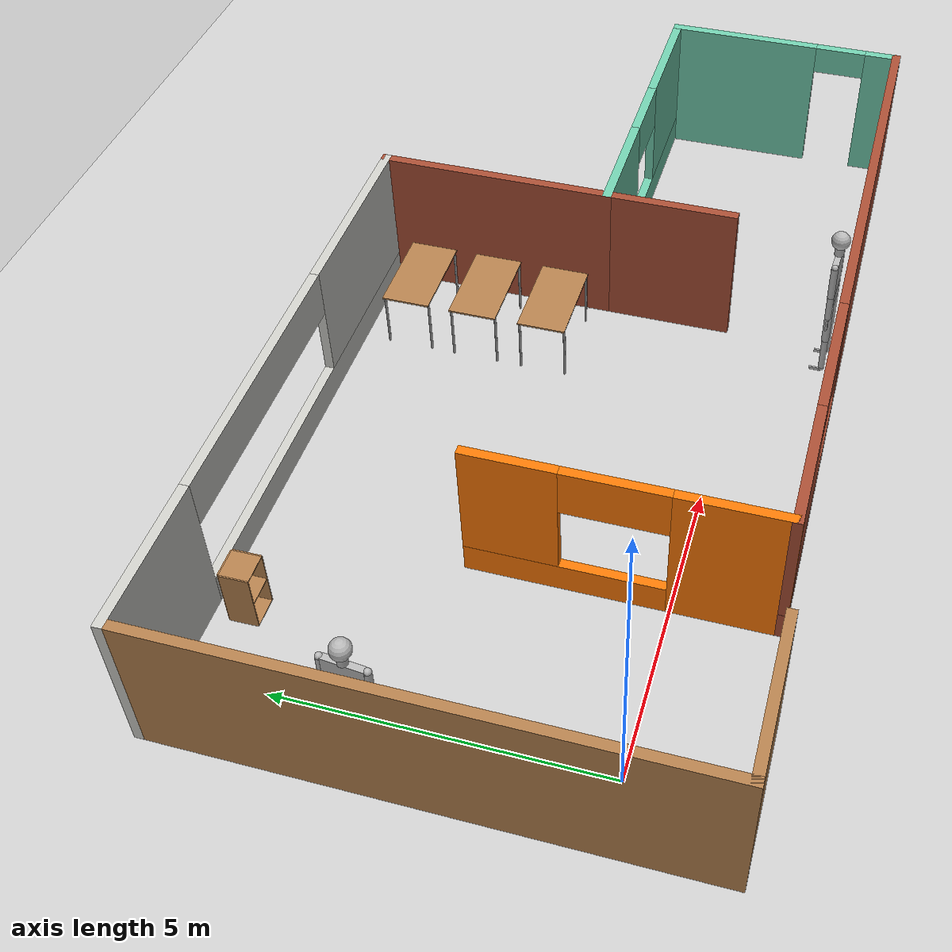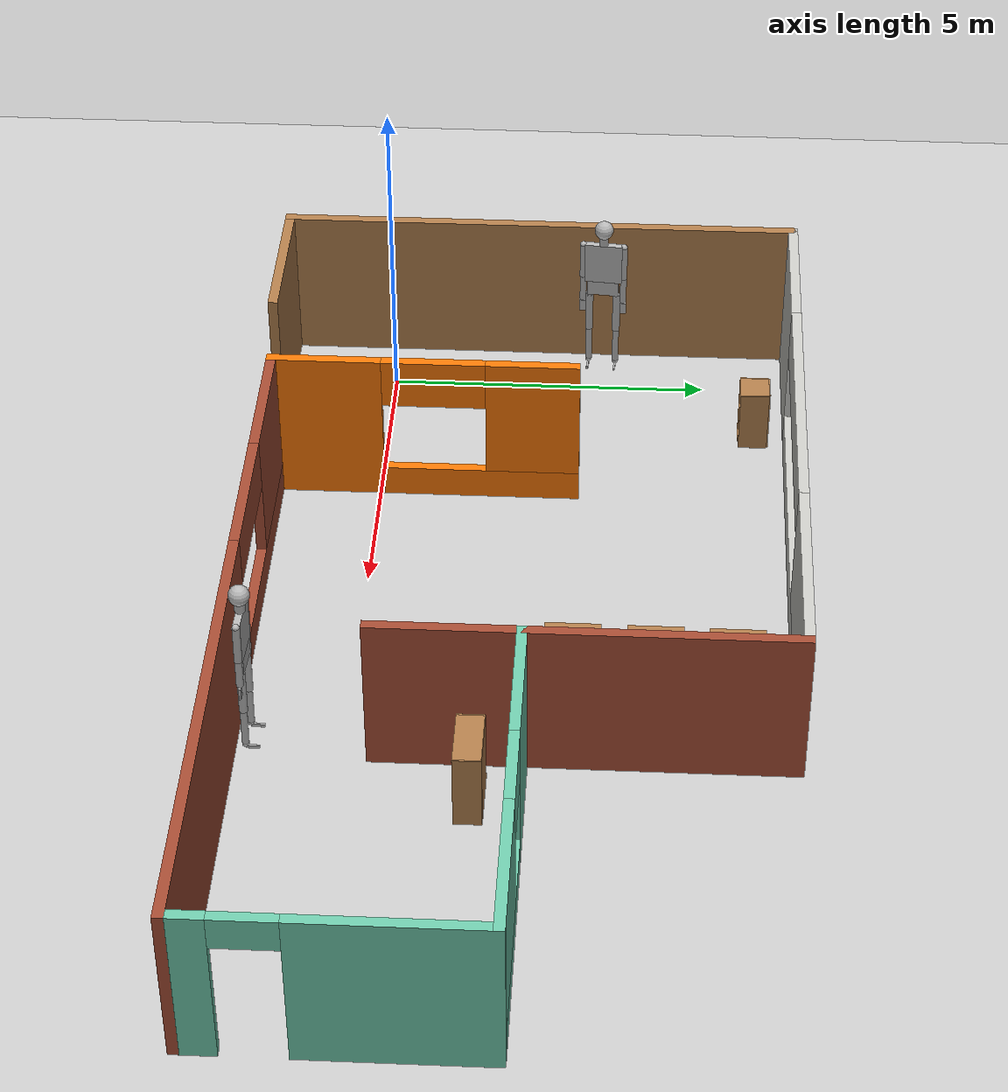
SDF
<sdf version="1.6">
 <world name="default">
  <light name="sun" type="directional">
   <pose>0 0 10 0 -0 0</pose>
   <diffuse>0.8 0.8 0.8 1</diffuse>
   <specular>0.2 0.2 0.2 1</specular>
   <attenuation>
    <range>1000</range>
    <constant>0.9</constant>
    <linear>0.01</linear>
    <quadratic>0.001</quadratic>
   </attenuation>
   <direction>-0.5 0.1 -0.9</direction>
  </light>
  <model name="ground_plane">
   <static>1</static>
   <link name="link">
    <collision name="collision">
     <geometry><plane><normal>0 0 1</normal><size>100 100</size></plane></geometry>
     <surface><friction><ode><mu>100</mu><mu2>50</mu2></ode></friction></surface>
    </collision>
    <visual name="visual">
     <cast_shadows>0</cast_shadows>
     <geometry><plane><normal>0 0 1</normal><size>100 100</size></plane></geometry>
     <material>
      <script><uri>file://media/materials/scripts/gazebo.material</uri><name>Gazebo/Grey</name></script>
     </material>
    </visual>
   </link>
  </model>
  <gravity>0 0 -9.8</gravity>
  <magnetic_field>6e-06 2.3e-05 -4.2e-05</magnetic_field>
  <atmosphere type="adiabatic"/>
  <physics name="default_physics" default="0" type="ode">
   <max_step_size>0.001</max_step_size>
   <real_time_factor>1</real_time_factor>
   <real_time_update_rate>1000</real_time_update_rate>
  </physics>
  <scene><ambient>0.4 0.4 0.4 1</ambient><background>0.7 0.7 0.7 1</background><shadows>1</shadows></scene>
  <spherical_coordinates>
   <surface_model>EARTH_WGS84</surface_model>
   <latitude_deg>0</latitude_deg>
   <longitude_deg>0</longitude_deg>
   <elevation>0</elevation>
   <heading_deg>0</heading_deg>
  </spherical_coordinates>
  <model name="my_room">
   <pose>6.60739 2.31299 0 0 -0 0</pose>
   <link name="Wall_1">
    <pose>-2.675 4.05 0 0 -0 0</pose>
    <visual name="Wall_1_Visual_0">
     <pose>-3.81694 0 1.25 0 -0 0</pose>
     <geometry><box><size>2.36613 0.15 2.5</size></box></geometry>
     <material>
      <script><uri>file://media/materials/scripts/gazebo.material</uri><name>Gazebo/CeilingTiled</name></script>
      <ambient>0.666667 0.333333 1 1</ambient>
     </material>
     <meta><layer>0</layer></meta>
    </visual>
    <collision name="Wall_1_Collision_0">
     <geometry><box><size>2.36613 0.15 2.5</size></box></geometry>
     <pose>-3.81694 0 1.25 0 -0 0</pose>
    </collision>
    <visual name="Wall_1_Visual_1">
     <pose>1.18306 0 0.25 0 -0 0</pose>
     <geometry><box><size>7.63387 0.15 0.5</size></box></geometry>
     <material>
      <script><uri>file://media/materials/scripts/gazebo.material</uri><name>Gazebo/CeilingTiled</name></script>
      <ambient>0.666667 0.333333 1 1</ambient>
     </material>
     <meta><layer>0</layer></meta>
    </visual>
    <collision name="Wall_1_Collision_1">
     <geometry><box><size>7.63387 0.15 0.5</size></box></geometry>
     <pose>1.18306 0 0.25 0 -0 0</pose>
    </collision>
    <visual name="Wall_1_Visual_2">
     <pose>3.39806 0 1.5 0 -0 0</pose>
     <geometry><box><size>3.20387 0.15 2</size></box></geometry>
     <material>
      <script><uri>file://media/materials/scripts/gazebo.material</uri><name>Gazebo/CeilingTiled</name></script>
      <ambient>0.666667 0.333333 1 1</ambient>
     </material>
     <meta><layer>0</layer></meta>
    </visual>
    <collision name="Wall_1_Collision_2">
     <geometry><box><size>3.20387 0.15 2</size></box></geometry>
     <pose>3.39806 0 1.5 0 -0 0</pose>
    </collision>
    <visual name="Wall_1_Visual_3">
     <pose>-0.418873 0 2.1 0 -0 0</pose>
     <geometry><box><size>4.43 0.15 0.8</size></box></geometry>
     <material>
      <script><uri>file://media/materials/scripts/gazebo.material</uri><name>Gazebo/CeilingTiled</name></script>
      <ambient>0.666667 0.333333 1 1</ambient>
     </material>
     <meta><layer>0</layer></meta>
    </visual>
    <collision name="Wall_1_Collision_3">
     <geometry><box><size>4.43 0.15 0.8</size></box></geometry>
     <pose>-0.418873 0 2.1 0 -0 0</pose>
    </collision>
   </link>
   <link name="Wall_15">
    <pose>-3.75 -1.6 0 0 -0 1.5708</pose>
    <visual name="Wall_15_Visual_0">
     <pose>-1.50843 0 1.25 0 -0 0</pose>
     <geometry><box><size>1.73314 0.15 2.5</size></box></geometry>
     <material>
      <script><uri>file://media/materials/scripts/gazebo.material</uri><name>Gazebo/Grey</name></script>
      <ambient>0.996078 0.47451 0.0196078 1</ambient>
     </material>
     <meta><layer>0</layer></meta>
    </visual>
    <collision name="Wall_15_Collision_0">
     <geometry><box><size>1.73314 0.15 2.5</size></box></geometry>
     <pose>-1.50843 0 1.25 0 -0 0</pose>
    </collision>
    <visual name="Wall_15_Visual_1">
     <pose>0.866573 0 0.25 0 -0 0</pose>
     <geometry><box><size>3.01686 0.15 0.5</size></box></geometry>
     <material>
      <script><uri>file://media/materials/scripts/gazebo.material</uri><name>Gazebo/Grey</name></script>
      <ambient>0.996078 0.47451 0.0196078 1</ambient>
     </material>
     <meta><layer>0</layer></meta>
    </visual>
    <collision name="Wall_15_Collision_1">
     <geometry><box><size>3.01686 0.15 0.5</size></box></geometry>
     <pose>0.866573 0 0.25 0 -0 0</pose>
    </collision>
    <visual name="Wall_15_Visual_2">
     <pose>1.65755 0 1.5 0 -0 0</pose>
     <geometry><box><size>1.43491 0.15 2</size></box></geometry>
     <material>
      <script><uri>file://media/materials/scripts/gazebo.material</uri><name>Gazebo/Grey</name></script>
      <ambient>0.996078 0.47451 0.0196078 1</ambient>
     </material>
     <meta><layer>0</layer></meta>
    </visual>
    <collision name="Wall_15_Collision_2">
     <geometry><box><size>1.43491 0.15 2</size></box></geometry>
     <pose>1.65755 0 1.5 0 -0 0</pose>
    </collision>
    <visual name="Wall_15_Visual_3">
     <pose>0.14912 0 2.1 0 -0 0</pose>
     <geometry><box><size>1.58195 0.15 0.8</size></box></geometry>
     <material>
      <script><uri>file://media/materials/scripts/gazebo.material</uri><name>Gazebo/Grey</name></script>
      <ambient>0.996078 0.47451 0.0196078 1</ambient>
     </material>
     <meta><layer>0</layer></meta>
    </visual>
    <collision name="Wall_15_Collision_3">
     <geometry><box><size>1.58195 0.15 0.8</size></box></geometry>
     <pose>0.14912 0 2.1 0 -0 0</pose>
    </collision>
   </link>
   <link name="Wall_17">
    <collision name="Wall_17_Collision">
     <geometry><box><size>8.25 0.15 2.5</size></box></geometry>
     <pose>0 0 1.25 0 -0 0</pose>
    </collision>
    <visual name="Wall_17_Visual">
     <pose>0 0 1.25 0 -0 0</pose>
     <geometry><box><size>8.25 0.15 2.5</size></box></geometry>
     <material>
      <script><uri>file://media/materials/scripts/gazebo.material</uri><name>Gazebo/Wood</name></script>
      <ambient>0.435294 0.796078 0.67451 1</ambient>
     </material>
     <meta><layer>0</layer></meta>
    </visual>
    <pose>-7.6 0 0 0 0 -1.5708</pose>
   </link>
   <link name="Wall_2">
    <collision name="Wall_2_Collision">
     <geometry><box><size>4 0.15 2.5</size></box></geometry>
     <pose>0 0 1.25 0 -0 0</pose>
    </collision>
    <visual name="Wall_2_Visual">
     <pose>0 0 1.25 0 -0 0</pose>
     <geometry><box><size>4 0.15 2.5</size></box></geometry>
     <material>
      <script><uri>file://media/materials/scripts/gazebo.material</uri><name>Gazebo/Bricks</name></script>
      <ambient>1 1 1 1</ambient>
     </material>
     <meta><layer>0</layer></meta>
    </visual>
    <pose>2.25 2.125 0 0 0 -1.5708</pose>
   </link>
   <link name="Wall_21">
    <collision name="Wall_21_Collision">
     <geometry><box><size>2.5 0.15 2.5</size></box></geometry>
     <pose>0 0 1.25 0 -0 0</pose>
    </collision>
    <visual name="Wall_21_Visual">
     <pose>0 0 1.25 0 -0 0</pose>
     <geometry><box><size>2.5 0.15 2.5</size></box></geometry>
     <material>
      <script><uri>file://media/materials/scripts/gazebo.material</uri><name>Gazebo/Wood</name></script>
      <ambient>1 1 1 1</ambient>
     </material>
     <meta><layer>0</layer></meta>
    </visual>
    <pose>-6.425 -4.05 0 0 -0 0</pose>
   </link>
   <link name="Wall_3">
    <pose>4.925 0.2 0 0 -0 0</pose>
    <visual name="Wall_3_Visual_0">
     <pose>-1.73801 0 1.25 0 -0 0</pose>
     <geometry><box><size>2.02399 0.15 2.5</size></box></geometry>
     <material>
      <script><uri>file://media/materials/scripts/gazebo.material</uri><name>Gazebo/Grey</name></script>
      <ambient>0.435294 0.796078 0.67451 1</ambient>
     </material>
     <meta><layer>0</layer></meta>
    </visual>
    <collision name="Wall_3_Collision_0">
     <geometry><box><size>2.02399 0.15 2.5</size></box></geometry>
     <pose>-1.73801 0 1.25 0 -0 0</pose>
    </collision>
    <visual name="Wall_3_Visual_1">
     <pose>1.01199 0 0.25 0 -0 0</pose>
     <geometry><box><size>3.47601 0.15 0.5</size></box></geometry>
     <material>
      <script><uri>file://media/materials/scripts/gazebo.material</uri><name>Gazebo/Grey</name></script>
      <ambient>0.435294 0.796078 0.67451 1</ambient>
     </material>
     <meta><layer>0</layer></meta>
    </visual>
    <collision name="Wall_3_Collision_1">
     <geometry><box><size>3.47601 0.15 0.5</size></box></geometry>
     <pose>1.01199 0 0.25 0 -0 0</pose>
    </collision>
    <visual name="Wall_3_Visual_2">
     <pose>1.63628 0 1.5 0 -0 0</pose>
     <geometry><box><size>2.22744 0.15 2</size></box></geometry>
     <material>
      <script><uri>file://media/materials/scripts/gazebo.material</uri><name>Gazebo/Grey</name></script>
      <ambient>0.435294 0.796078 0.67451 1</ambient>
     </material>
     <meta><layer>0</layer></meta>
    </visual>
    <collision name="Wall_3_Collision_2">
     <geometry><box><size>2.22744 0.15 2</size></box></geometry>
     <pose>1.63628 0 1.5 0 -0 0</pose>
    </collision>
    <visual name="Wall_3_Visual_3">
     <pose>-0.101725 0 2.1 0 -0 0</pose>
     <geometry><box><size>1.24858 0.15 0.8</size></box></geometry>
     <material>
      <script><uri>file://media/materials/scripts/gazebo.material</uri><name>Gazebo/Grey</name></script>
      <ambient>0.435294 0.796078 0.67451 1</ambient>
     </material>
     <meta><layer>0</layer></meta>
    </visual>
    <collision name="Wall_3_Collision_3">
     <geometry><box><size>1.24858 0.15 0.8</size></box></geometry>
     <pose>-0.101725 0 2.1 0 -0 0</pose>
    </collision>
   </link>
   <link name="Wall_4">
    <pose>7.6 -1.85 0 0 0 -1.5708</pose>
    <visual name="Wall_4_Visual_0">
     <pose>-0.769041 0 1.25 0 -0 0</pose>
     <geometry><box><size>2.71192 0.15 2.5</size></box></geometry>
     <material>
      <script><uri>file://media/materials/scripts/gazebo.material</uri><name>Gazebo/Grey</name></script>
      <ambient>0.435294 0.796078 0.67451 1</ambient>
     </material>
     <meta><layer>0</layer></meta>
    </visual>
    <collision name="Wall_4_Collision_0">
     <geometry><box><size>2.71192 0.15 2.5</size></box></geometry>
     <pose>-0.769041 0 1.25 0 -0 0</pose>
    </collision>
    <visual name="Wall_4_Visual_1">
     <pose>1.80596 0 1.25 0 -0 0</pose>
     <geometry><box><size>0.638081 0.15 2.5</size></box></geometry>
     <material>
      <script><uri>file://media/materials/scripts/gazebo.material</uri><name>Gazebo/Grey</name></script>
      <ambient>0.435294 0.796078 0.67451 1</ambient>
     </material>
     <meta><layer>0</layer></meta>
    </visual>
    <collision name="Wall_4_Collision_1">
     <geometry><box><size>0.638081 0.15 2.5</size></box></geometry>
     <pose>1.80596 0 1.25 0 -0 0</pose>
    </collision>
    <visual name="Wall_4_Visual_2">
     <pose>1.03692 0 2.25 0 -0 0</pose>
     <geometry><box><size>0.9 0.15 0.5</size></box></geometry>
     <material>
      <script><uri>file://media/materials/scripts/gazebo.material</uri><name>Gazebo/Grey</name></script>
      <ambient>0.435294 0.796078 0.67451 1</ambient>
     </material>
     <meta><layer>0</layer></meta>
    </visual>
    <collision name="Wall_4_Collision_2">
     <geometry><box><size>0.9 0.15 0.5</size></box></geometry>
     <pose>1.03692 0 2.25 0 -0 0</pose>
    </collision>
   </link>
   <link name="Wall_5">
    <pose>1.925 -3.9 0 0 -0 3.14159</pose>
    <visual name="Wall_5_Visual_0">
     <pose>-2.20932 0 1.25 0 -0 0</pose>
     <geometry><box><size>7.08135 0.15 2.5</size></box></geometry>
     <material>
      <script><uri>file://media/materials/scripts/gazebo.material</uri><name>Gazebo/Bricks</name></script>
      <ambient>1 1 1 1</ambient>
     </material>
     <meta><layer>0</layer></meta>
    </visual>
    <collision name="Wall_5_Collision_0">
     <geometry><box><size>7.08135 0.15 2.5</size></box></geometry>
     <pose>-2.20932 0 1.25 0 -0 0</pose>
    </collision>
    <visual name="Wall_5_Visual_1">
     <pose>3.54068 0 0.25 0 -0 0</pose>
     <geometry><box><size>4.41865 0.15 0.5</size></box></geometry>
     <material>
      <script><uri>file://media/materials/scripts/gazebo.material</uri><name>Gazebo/Bricks</name></script>
      <ambient>1 1 1 1</ambient>
     </material>
     <meta><layer>0</layer></meta>
    </visual>
    <collision name="Wall_5_Collision_1">
     <geometry><box><size>4.41865 0.15 0.5</size></box></geometry>
     <pose>3.54068 0 0.25 0 -0 0</pose>
    </collision>
    <visual name="Wall_5_Visual_2">
     <pose>4.64744 0 1.5 0 -0 0</pose>
     <geometry><box><size>2.20512 0.15 2</size></box></geometry>
     <material>
      <script><uri>file://media/materials/scripts/gazebo.material</uri><name>Gazebo/Bricks</name></script>
      <ambient>1 1 1 1</ambient>
     </material>
     <meta><layer>0</layer></meta>
    </visual>
    <collision name="Wall_5_Collision_2">
     <geometry><box><size>2.20512 0.15 2</size></box></geometry>
     <pose>4.64744 0 1.5 0 -0 0</pose>
    </collision>
    <visual name="Wall_5_Visual_3">
     <pose>2.43811 0 2.1 0 -0 0</pose>
     <geometry><box><size>2.21352 0.15 0.8</size></box></geometry>
     <material>
      <script><uri>file://media/materials/scripts/gazebo.material</uri><name>Gazebo/Bricks</name></script>
      <ambient>1 1 1 1</ambient>
     </material>
     <meta><layer>0</layer></meta>
    </visual>
    <collision name="Wall_5_Collision_3">
     <geometry><box><size>2.21352 0.15 0.8</size></box></geometry>
     <pose>2.43811 0 2.1 0 -0 0</pose>
    </collision>
   </link>
   <link name="Wall_7">
    <collision name="Wall_7_Collision">
     <geometry><box><size>2.25 0.15 2.5</size></box></geometry>
     <pose>0 0 1.25 0 -0 0</pose>
    </collision>
    <visual name="Wall_7_Visual">
     <pose>0 0 1.25 0 -0 0</pose>
     <geometry><box><size>2.25 0.15 2.5</size></box></geometry>
     <material>
      <script><uri>file://media/materials/scripts/gazebo.material</uri><name>Gazebo/Bricks</name></script>
      <ambient>1 1 1 1</ambient>
     </material>
     <meta><layer>0</layer></meta>
    </visual>
    <pose>2.25 -0.85 0 0 0 -1.5708</pose>
   </link>
   <static>1</static>
  </model>
  <model name="bookshelf">
   <static>1</static>
   <link name="link">
    <inertial><mass>1</mass></inertial>
    <collision name="back">
     <pose>0 0.005 0.6 0 -0 0</pose>
     <geometry><box><size>0.9 0.01 1.2</size></box></geometry>
    </collision>
    <visual name="visual1">
     <pose>0 0.005 0.6 0 -0 0</pose>
     <geometry><box><size>0.9 0.01 1.2</size></box></geometry>
     <material>
      <script><uri>file://media/materials/scripts/gazebo.material</uri><name>Gazebo/Wood</name></script>
     </material>
    </visual>
    <collision name="left_side">
     <pose>0.45 -0.195 0.6 0 -0 0</pose>
     <geometry><box><size>0.02 0.4 1.2</size></box></geometry>
    </collision>
    <visual name="visual2">
     <pose>0.45 -0.195 0.6 0 -0 0</pose>
     <geometry><box><size>0.02 0.4 1.2</size></box></geometry>
     <material>
      <script><uri>file://media/materials/scripts/gazebo.material</uri><name>Gazebo/Wood</name></script>
     </material>
    </visual>
    <collision name="right_side">
     <pose>-0.45 -0.195 0.6 0 -0 0</pose>
     <geometry><box><size>0.02 0.4 1.2</size></box></geometry>
    </collision>
    <visual name="visual3">
     <pose>-0.45 -0.195 0.6 0 -0 0</pose>
     <geometry><box><size>0.02 0.4 1.2</size></box></geometry>
     <material>
      <script><uri>file://media/materials/scripts/gazebo.material</uri><name>Gazebo/Wood</name></script>
     </material>
    </visual>
    <collision name="bottom">
     <pose>0 -0.195 0.03 0 -0 0</pose>
     <geometry><box><size>0.88 0.4 0.06</size></box></geometry>
    </collision>
    <visual name="visual4">
     <pose>0 -0.195 0.03 0 -0 0</pose>
     <geometry><box><size>0.88 0.4 0.06</size></box></geometry>
     <material>
      <script><uri>file://media/materials/scripts/gazebo.material</uri><name>Gazebo/Wood</name></script>
     </material>
    </visual>
    <collision name="top">
     <pose>0 -0.195 1.19 0 -0 0</pose>
     <geometry><box><size>0.88 0.4 0.02</size></box></geometry>
    </collision>
    <visual name="visual5">
     <pose>0 -0.195 1.19 0 -0 0</pose>
     <geometry><box><size>0.88 0.4 0.02</size></box></geometry>
     <material>
      <script><uri>file://media/materials/scripts/gazebo.material</uri><name>Gazebo/Wood</name></script>
     </material>
    </visual>
    <collision name="low_shelf">
     <pose>0 -0.195 0.43 0 -0 0</pose>
     <geometry><box><size>0.88 0.4 0.02</size></box></geometry>
    </collision>
    <visual name="visual6">
     <pose>0 -0.195 0.43 0 -0 0</pose>
     <geometry><box><size>0.88 0.4 0.02</size></box></geometry>
     <material>
      <script><uri>file://media/materials/scripts/gazebo.material</uri><name>Gazebo/Wood</name></script>
     </material>
    </visual>
    <collision name="high_shelf">
     <pose>0 -0.195 0.8 0 -0 0</pose>
     <geometry><box><size>0.88 0.4 0.02</size></box></geometry>
    </collision>
    <visual name="visual7">
     <pose>0 -0.195 0.8 0 -0 0</pose>
     <geometry><box><size>0.88 0.4 0.02</size></box></geometry>
     <material>
      <script><uri>file://media/materials/scripts/gazebo.material</uri><name>Gazebo/Wood</name></script>
     </material>
    </visual>
   </link>
   <pose>9.62343 2.02293 0 0 -0 0</pose>
  </model>
  <model name="table">
   <static>1</static>
   <link name="link">
    <collision name="surface">
     <pose>0 0 1 0 -0 0</pose>
     <geometry><box><size>1.5 0.8 0.03</size></box></geometry>
     <surface><friction><ode><mu>0.6</mu><mu2>0.6</mu2></ode></friction></surface>
    </collision>
    <visual name="visual1">
     <pose>0 0 1 0 -0 0</pose>
     <geometry><box><size>1.5 0.8 0.03</size></box></geometry>
     <material>
      <script><uri>file://media/materials/scripts/gazebo.material</uri><name>Gazebo/Wood</name></script>
     </material>
    </visual>
    <collision name="front_left_leg">
     <pose>0.68 0.38 0.5 0 -0 0</pose>
     <geometry><cylinder><radius>0.02</radius><length>1</length></cylinder></geometry>
    </collision>
    <visual name="front_left_leg">
     <pose>0.68 0.38 0.5 0 -0 0</pose>
     <geometry><cylinder><radius>0.02</radius><length>1</length></cylinder></geometry>
     <material>
      <script><uri>file://media/materials/scripts/gazebo.material</uri><name>Gazebo/Grey</name></script>
     </material>
    </visual>
    <collision name="front_right_leg">
     <pose>0.68 -0.38 0.5 0 -0 0</pose>
     <geometry><cylinder><radius>0.02</radius><length>1</length></cylinder></geometry>
    </collision>
    <visual name="front_right_leg">
     <pose>0.68 -0.38 0.5 0 -0 0</pose>
     <geometry><cylinder><radius>0.02</radius><length>1</length></cylinder></geometry>
     <material>
      <script><uri>file://media/materials/scripts/gazebo.material</uri><name>Gazebo/Grey</name></script>
     </material>
    </visual>
    <collision name="back_right_leg">
     <pose>-0.68 -0.38 0.5 0 -0 0</pose>
     <geometry><cylinder><radius>0.02</radius><length>1</length></cylinder></geometry>
    </collision>
    <visual name="back_right_leg">
     <pose>-0.68 -0.38 0.5 0 -0 0</pose>
     <geometry><cylinder><radius>0.02</radius><length>1</length></cylinder></geometry>
     <material>
      <script><uri>file://media/materials/scripts/gazebo.material</uri><name>Gazebo/Grey</name></script>
     </material>
    </visual>
    <collision name="back_left_leg">
     <pose>-0.68 0.38 0.5 0 -0 0</pose>
     <geometry><cylinder><radius>0.02</radius><length>1</length></cylinder></geometry>
    </collision>
    <visual name="back_left_leg">
     <pose>-0.68 0.38 0.5 0 -0 0</pose>
     <geometry><cylinder><radius>0.02</radius><length>1</length></cylinder></geometry>
     <material>
      <script><uri>file://media/materials/scripts/gazebo.material</uri><name>Gazebo/Grey</name></script>
     </material>
    </visual>
   </link>
   <pose>7.7757 5.48796 0 0 -0 0</pose>
  </model>
  <model name="table_0">
   <static>1</static>
   <link name="link">
    <collision name="surface">
     <pose>0 0 1 0 -0 0</pose>
     <geometry><box><size>1.5 0.8 0.03</size></box></geometry>
     <surface><friction><ode><mu>0.6</mu><mu2>0.6</mu2></ode></friction></surface>
    </collision>
    <visual name="visual1">
     <pose>0 0 1 0 -0 0</pose>
     <geometry><box><size>1.5 0.8 0.03</size></box></geometry>
     <material>
      <script><uri>file://media/materials/scripts/gazebo.material</uri><name>Gazebo/Wood</name></script>
     </material>
    </visual>
    <collision name="front_left_leg">
     <pose>0.68 0.38 0.5 0 -0 0</pose>
     <geometry><cylinder><radius>0.02</radius><length>1</length></cylinder></geometry>
    </collision>
    <visual name="front_left_leg">
     <pose>0.68 0.38 0.5 0 -0 0</pose>
     <geometry><cylinder><radius>0.02</radius><length>1</length></cylinder></geometry>
     <material>
      <script><uri>file://media/materials/scripts/gazebo.material</uri><name>Gazebo/Grey</name></script>
     </material>
    </visual>
    <collision name="front_right_leg">
     <pose>0.68 -0.38 0.5 0 -0 0</pose>
     <geometry><cylinder><radius>0.02</radius><length>1</length></cylinder></geometry>
    </collision>
    <visual name="front_right_leg">
     <pose>0.68 -0.38 0.5 0 -0 0</pose>
     <geometry><cylinder><radius>0.02</radius><length>1</length></cylinder></geometry>
     <material>
      <script><uri>file://media/materials/scripts/gazebo.material</uri><name>Gazebo/Grey</name></script>
     </material>
    </visual>
    <collision name="back_right_leg">
     <pose>-0.68 -0.38 0.5 0 -0 0</pose>
     <geometry><cylinder><radius>0.02</radius><length>1</length></cylinder></geometry>
    </collision>
    <visual name="back_right_leg">
     <pose>-0.68 -0.38 0.5 0 -0 0</pose>
     <geometry><cylinder><radius>0.02</radius><length>1</length></cylinder></geometry>
     <material>
      <script><uri>file://media/materials/scripts/gazebo.material</uri><name>Gazebo/Grey</name></script>
     </material>
    </visual>
    <collision name="back_left_leg">
     <pose>-0.68 0.38 0.5 0 -0 0</pose>
     <geometry><cylinder><radius>0.02</radius><length>1</length></cylinder></geometry>
    </collision>
    <visual name="back_left_leg">
     <pose>-0.68 0.38 0.5 0 -0 0</pose>
     <geometry><cylinder><radius>0.02</radius><length>1</length></cylinder></geometry>
     <material>
      <script><uri>file://media/materials/scripts/gazebo.material</uri><name>Gazebo/Grey</name></script>
     </material>
    </visual>
   </link>
   <pose>7.76626 4.32656 0 0 -0 0</pose>
  </model>
  <model name="table_1">
   <static>1</static>
   <link name="link">
    <collision name="surface">
     <pose>0 0 1 0 -0 0</pose>
     <geometry><box><size>1.5 0.8 0.03</size></box></geometry>
     <surface><friction><ode><mu>0.6</mu><mu2>0.6</mu2></ode></friction></surface>
    </collision>
    <visual name="visual1">
     <pose>0 0 1 0 -0 0</pose>
     <geometry><box><size>1.5 0.8 0.03</size></box></geometry>
     <material>
      <script><uri>file://media/materials/scripts/gazebo.material</uri><name>Gazebo/Wood</name></script>
     </material>
    </visual>
    <collision name="front_left_leg">
     <pose>0.68 0.38 0.5 0 -0 0</pose>
     <geometry><cylinder><radius>0.02</radius><length>1</length></cylinder></geometry>
    </collision>
    <visual name="front_left_leg">
     <pose>0.68 0.38 0.5 0 -0 0</pose>
     <geometry><cylinder><radius>0.02</radius><length>1</length></cylinder></geometry>
     <material>
      <script><uri>file://media/materials/scripts/gazebo.material</uri><name>Gazebo/Grey</name></script>
     </material>
    </visual>
    <collision name="front_right_leg">
     <pose>0.68 -0.38 0.5 0 -0 0</pose>
     <geometry><cylinder><radius>0.02</radius><length>1</length></cylinder></geometry>
    </collision>
    <visual name="front_right_leg">
     <pose>0.68 -0.38 0.5 0 -0 0</pose>
     <geometry><cylinder><radius>0.02</radius><length>1</length></cylinder></geometry>
     <material>
      <script><uri>file://media/materials/scripts/gazebo.material</uri><name>Gazebo/Grey</name></script>
     </material>
    </visual>
    <collision name="back_right_leg">
     <pose>-0.68 -0.38 0.5 0 -0 0</pose>
     <geometry><cylinder><radius>0.02</radius><length>1</length></cylinder></geometry>
    </collision>
    <visual name="back_right_leg">
     <pose>-0.68 -0.38 0.5 0 -0 0</pose>
     <geometry><cylinder><radius>0.02</radius><length>1</length></cylinder></geometry>
     <material>
      <script><uri>file://media/materials/scripts/gazebo.material</uri><name>Gazebo/Grey</name></script>
     </material>
    </visual>
    <collision name="back_left_leg">
     <pose>-0.68 0.38 0.5 0 -0 0</pose>
     <geometry><cylinder><radius>0.02</radius><length>1</length></cylinder></geometry>
    </collision>
    <visual name="back_left_leg">
     <pose>-0.68 0.38 0.5 0 -0 0</pose>
     <geometry><cylinder><radius>0.02</radius><length>1</length></cylinder></geometry>
     <material>
      <script><uri>file://media/materials/scripts/gazebo.material</uri><name>Gazebo/Grey</name></script>
     </material>
    </visual>
   </link>
   <pose>7.76108 3.1442 0 0 -0 0</pose>
  </model>
  <model name="ragdoll">
   <pose>-0.670559 3.34416 1.3998 -0.000108 0.010915 -0.090686</pose>
   <link name="hip">
    <inertial>
     <inertia><ixx>0.1</ixx><ixy>0</ixy><ixz>0</ixz><iyy>0.1</iyy><iyz>0</iyz><izz>0.1</izz></inertia>
     <mass>10</mass>
    </inertial>
    <collision name="hip_geom">
     <pose>0 0 0.125 0 -0 0</pose>
     <geometry><box><size>0.1 0.5 0.25</size></box></geometry>
     <surface>
      <friction><ode><mu>-1</mu><mu2>-1</mu2><fdir1>0 0 0</fdir1><slip1>0</slip1><slip2>0</slip2></ode></friction>
      <bounce><restitution_coefficient>0</restitution_coefficient><threshold>100000</threshold></bounce>
      <contact>
       <ode>
        <soft_cfm>0</soft_cfm>
        <soft_erp>0.2</soft_erp>
        <kp>1e+12</kp>
        <kd>1</kd>
        <max_vel>0</max_vel>
        <min_depth>0.001</min_depth>
       </ode>
      </contact>
     </surface>
    </collision>
    <visual name="hip_geom_visual">
     <pose>0 0 0.125 0 -0 0</pose>
     <geometry><box><size>0.1 0.5 0.25</size></box></geometry>
    </visual>
    <gravity>0</gravity>
   </link>
   <link name="l_thigh_pan">
    <pose>0 0.22 0 0 -0 0</pose>
    <inertial>
     <inertia><ixx>0.01</ixx><ixy>0</ixy><ixz>0</ixz><iyy>0.01</iyy><iyz>0</iyz><izz>0.01</izz></inertia>
     <mass>1</mass>
    </inertial>
    <collision name="l_thigh_pan_geom">
     <pose>0 0 -0.03 0 -0 0</pose>
     <geometry><sphere><radius>0.06</radius></sphere></geometry>
     <surface>
      <friction><ode><mu>-1</mu><mu2>-1</mu2><fdir1>0 0 0</fdir1><slip1>0</slip1><slip2>0</slip2></ode></friction>
      <bounce><restitution_coefficient>0</restitution_coefficient><threshold>100000</threshold></bounce>
      <contact>
       <ode>
        <soft_cfm>0</soft_cfm>
        <soft_erp>0.2</soft_erp>
        <kp>1e+12</kp>
        <kd>1</kd>
        <max_vel>0</max_vel>
        <min_depth>0.001</min_depth>
       </ode>
      </contact>
     </surface>
    </collision>
    <visual name="l_thigh_pan_geom_visual">
     <pose>0 0 -0.03 0 -0 0</pose>
     <geometry><sphere><radius>0.06</radius></sphere></geometry>
    </visual>
    <gravity>0</gravity>
   </link>
   <link name="l_thigh_lift">
    <pose>0 0.22 0 0 -0 0</pose>
    <inertial>
     <inertia><ixx>0.05</ixx><ixy>0</ixy><ixz>0</ixz><iyy>0.05</iyy><iyz>0</iyz><izz>0.05</izz></inertia>
     <mass>5</mass>
    </inertial>
    <collision name="l_thigh_lift_geom">
     <pose>0 0 -0.35 0 -0 0</pose>
     <geometry><cylinder><radius>0.06</radius><length>0.7</length></cylinder></geometry>
     <surface>
      <friction><ode><mu>-1</mu><mu2>-1</mu2><fdir1>0 0 0</fdir1><slip1>0</slip1><slip2>0</slip2></ode></friction>
      <bounce><restitution_coefficient>0</restitution_coefficient><threshold>100000</threshold></bounce>
      <contact>
       <ode>
        <soft_cfm>0</soft_cfm>
        <soft_erp>0.2</soft_erp>
        <kp>1e+12</kp>
        <kd>1</kd>
        <max_vel>0</max_vel>
        <min_depth>0.001</min_depth>
       </ode>
      </contact>
     </surface>
    </collision>
    <visual name="l_thigh_lift_geom_visual">
     <pose>0 0 -0.35 0 -0 0</pose>
     <geometry><cylinder><radius>0.06</radius><length>0.7</length></cylinder></geometry>
    </visual>
    <gravity>0</gravity>
   </link>
   <link name="l_calf">
    <pose>0 0.22 -0.7 0 -0 0</pose>
    <inertial>
     <inertia><ixx>0.02</ixx><ixy>0</ixy><ixz>0</ixz><iyy>0.02</iyy><iyz>0</iyz><izz>0.02</izz></inertia>
     <mass>2</mass>
    </inertial>
    <collision name="l_calf_geom">
     <pose>0 0 -0.3 0 -0 0</pose>
     <geometry><cylinder><radius>0.05</radius><length>0.6</length></cylinder></geometry>
     <surface>
      <friction><ode><mu>-1</mu><mu2>-1</mu2><fdir1>0 0 0</fdir1><slip1>0</slip1><slip2>0</slip2></ode></friction>
      <bounce><restitution_coefficient>0</restitution_coefficient><threshold>100000</threshold></bounce>
      <contact>
       <ode>
        <soft_cfm>0</soft_cfm>
        <soft_erp>0.2</soft_erp>
        <kp>1e+12</kp>
        <kd>1</kd>
        <max_vel>0</max_vel>
        <min_depth>0.001</min_depth>
       </ode>
      </contact>
     </surface>
    </collision>
    <visual name="l_calf_geom_visual">
     <pose>0 0 -0.3 0 -0 0</pose>
     <geometry><cylinder><radius>0.05</radius><length>0.6</length></cylinder></geometry>
    </visual>
    <gravity>0</gravity>
   </link>
   <link name="l_ankle">
    <pose>0 0.22 -1.325 0 -0 0</pose>
    <inertial>
     <inertia><ixx>0.01</ixx><ixy>0</ixy><ixz>0</ixz><iyy>0.01</iyy><iyz>0</iyz><izz>0.01</izz></inertia>
     <mass>1</mass>
    </inertial>
    <collision name="l_ankle_geom">
     <geometry><sphere><radius>0.05</radius></sphere></geometry>
     <surface>
      <friction><ode><mu>-1</mu><mu2>-1</mu2><fdir1>0 0 0</fdir1><slip1>0</slip1><slip2>0</slip2></ode></friction>
      <bounce><restitution_coefficient>0</restitution_coefficient><threshold>100000</threshold></bounce>
      <contact>
       <ode>
        <soft_cfm>0</soft_cfm>
        <soft_erp>0.2</soft_erp>
        <kp>1e+12</kp>
        <kd>1</kd>
        <max_vel>0</max_vel>
        <min_depth>0.001</min_depth>
       </ode>
      </contact>
     </surface>
    </collision>
    <visual name="l_ankle_geom_visual"><geometry><sphere><radius>0.05</radius></sphere></geometry></visual>
    <gravity>0</gravity>
   </link>
   <link name="l_foot">
    <pose>0 0.22 -1.35 0 -0 0</pose>
    <inertial>
     <pose>0.1 0 0 0 -0 0</pose>
     <inertia><ixx>0.01</ixx><ixy>0</ixy><ixz>0</ixz><iyy>0.01</iyy><iyz>0</iyz><izz>0.01</izz></inertia>
     <mass>1</mass>
    </inertial>
    <collision name="l_foot_geom">
     <pose>0.1 0 -0.025 0 -0 0</pose>
     <geometry><box><size>0.2 0.03 0.05</size></box></geometry>
     <surface>
      <friction><ode><mu>-1</mu><mu2>-1</mu2><fdir1>0 0 0</fdir1><slip1>0</slip1><slip2>0</slip2></ode></friction>
      <bounce><restitution_coefficient>0</restitution_coefficient><threshold>100000</threshold></bounce>
      <contact>
       <ode>
        <soft_cfm>0</soft_cfm>
        <soft_erp>0.2</soft_erp>
        <kp>1e+12</kp>
        <kd>1</kd>
        <max_vel>0</max_vel>
        <min_depth>0.001</min_depth>
       </ode>
      </contact>
     </surface>
    </collision>
    <visual name="l_foot_geom_visual">
     <pose>0.1 0 -0.025 0 -0 0</pose>
     <geometry><box><size>0.2 0.03 0.05</size></box></geometry>
    </visual>
   </link>
   <link name="r_thigh_pan">
    <pose>0 -0.22 0 0 -0 0</pose>
    <inertial>
     <inertia><ixx>0.01</ixx><ixy>0</ixy><ixz>0</ixz><iyy>0.01</iyy><iyz>0</iyz><izz>0.01</izz></inertia>
     <mass>1</mass>
    </inertial>
    <collision name="r_thigh_pan_geom">
     <pose>0 0 -0.03 0 -0 0</pose>
     <geometry><sphere><radius>0.06</radius></sphere></geometry>
     <surface>
      <friction><ode><mu>-1</mu><mu2>-1</mu2><fdir1>0 0 0</fdir1><slip1>0</slip1><slip2>0</slip2></ode></friction>
      <bounce><restitution_coefficient>0</restitution_coefficient><threshold>100000</threshold></bounce>
      <contact>
       <ode>
        <soft_cfm>0</soft_cfm>
        <soft_erp>0.2</soft_erp>
        <kp>1e+12</kp>
        <kd>1</kd>
        <max_vel>0</max_vel>
        <min_depth>0.001</min_depth>
       </ode>
      </contact>
     </surface>
    </collision>
    <visual name="r_thigh_pan_geom_visual">
     <pose>0 0 -0.03 0 -0 0</pose>
     <geometry><sphere><radius>0.06</radius></sphere></geometry>
    </visual>
    <gravity>0</gravity>
   </link>
   <link name="r_thigh_lift">
    <pose>0 -0.22 0 0 -0 0</pose>
    <inertial>
     <inertia><ixx>0.05</ixx><ixy>0</ixy><ixz>0</ixz><iyy>0.05</iyy><iyz>0</iyz><izz>0.05</izz></inertia>
     <mass>5</mass>
    </inertial>
    <collision name="r_thigh_lift_geom">
     <pose>0 0 -0.35 0 -0 0</pose>
     <geometry><cylinder><radius>0.06</radius><length>0.7</length></cylinder></geometry>
     <surface>
      <friction><ode><mu>-1</mu><mu2>-1</mu2><fdir1>0 0 0</fdir1><slip1>0</slip1><slip2>0</slip2></ode></friction>
      <bounce><restitution_coefficient>0</restitution_coefficient><threshold>100000</threshold></bounce>
      <contact>
       <ode>
        <soft_cfm>0</soft_cfm>
        <soft_erp>0.2</soft_erp>
        <kp>1e+12</kp>
        <kd>1</kd>
        <max_vel>0</max_vel>
        <min_depth>0.001</min_depth>
       </ode>
      </contact>
     </surface>
    </collision>
    <visual name="r_thigh_lift_geom_visual">
     <pose>0 0 -0.35 0 -0 0</pose>
     <geometry><cylinder><radius>0.06</radius><length>0.7</length></cylinder></geometry>
    </visual>
    <gravity>0</gravity>
   </link>
   <link name="r_calf">
    <pose>0 -0.22 -0.7 0 -0 0</pose>
    <inertial>
     <inertia><ixx>0.02</ixx><ixy>0</ixy><ixz>0</ixz><iyy>0.02</iyy><iyz>0</iyz><izz>0.02</izz></inertia>
     <mass>2</mass>
    </inertial>
    <collision name="r_calf_geom">
     <pose>0 0 -0.3 0 -0 0</pose>
     <geometry><cylinder><radius>0.05</radius><length>0.6</length></cylinder></geometry>
     <surface>
      <friction><ode><mu>-1</mu><mu2>-1</mu2><fdir1>0 0 0</fdir1><slip1>0</slip1><slip2>0</slip2></ode></friction>
      <bounce><restitution_coefficient>0</restitution_coefficient><threshold>100000</threshold></bounce>
      <contact>
       <ode>
        <soft_cfm>0</soft_cfm>
        <soft_erp>0.2</soft_erp>
        <kp>1e+12</kp>
        <kd>1</kd>
        <max_vel>0</max_vel>
        <min_depth>0.001</min_depth>
       </ode>
      </contact>
     </surface>
    </collision>
    <visual name="r_calf_geom_visual">
     <pose>0 0 -0.3 0 -0 0</pose>
     <geometry><cylinder><radius>0.05</radius><length>0.6</length></cylinder></geometry>
    </visual>
    <gravity>0</gravity>
   </link>
   <link name="r_ankle">
    <pose>0 -0.22 -1.325 0 -0 0</pose>
    <inertial>
     <inertia><ixx>0.01</ixx><ixy>0</ixy><ixz>0</ixz><iyy>0.01</iyy><iyz>0</iyz><izz>0.01</izz></inertia>
     <mass>1</mass>
    </inertial>
    <collision name="r_ankle_geom">
     <geometry><sphere><radius>0.05</radius></sphere></geometry>
     <surface>
      <friction><ode><mu>-1</mu><mu2>-1</mu2><fdir1>0 0 0</fdir1><slip1>0</slip1><slip2>0</slip2></ode></friction>
      <bounce><restitution_coefficient>0</restitution_coefficient><threshold>100000</threshold></bounce>
      <contact>
       <ode>
        <soft_cfm>0</soft_cfm>
        <soft_erp>0.2</soft_erp>
        <kp>1e+12</kp>
        <kd>1</kd>
        <max_vel>0</max_vel>
        <min_depth>0.001</min_depth>
       </ode>
      </contact>
     </surface>
    </collision>
    <visual name="r_ankle_geom_visual"><geometry><sphere><radius>0.05</radius></sphere></geometry></visual>
    <gravity>0</gravity>
   </link>
   <link name="r_foot">
    <pose>0 -0.22 -1.35 0 -0 0</pose>
    <inertial>
     <pose>0.1 0 0 0 -0 0</pose>
     <inertia><ixx>0.01</ixx><ixy>0</ixy><ixz>0</ixz><iyy>0.01</iyy><iyz>0</iyz><izz>0.01</izz></inertia>
     <mass>1</mass>
    </inertial>
    <collision name="r_foot_geom">
     <pose>0.1 0 -0.025 0 -0 0</pose>
     <geometry><box><size>0.2 0.03 0.05</size></box></geometry>
     <surface>
      <friction><ode><mu>-1</mu><mu2>-1</mu2><fdir1>0 0 0</fdir1><slip1>0</slip1><slip2>0</slip2></ode></friction>
      <bounce><restitution_coefficient>0</restitution_coefficient><threshold>100000</threshold></bounce>
      <contact>
       <ode>
        <soft_cfm>0</soft_cfm>
        <soft_erp>0.2</soft_erp>
        <kp>1e+12</kp>
        <kd>1</kd>
        <max_vel>0</max_vel>
        <min_depth>0.001</min_depth>
       </ode>
      </contact>
     </surface>
    </collision>
    <visual name="r_foot_geom_visual">
     <pose>0.1 0 -0.025 0 -0 0</pose>
     <geometry><box><size>0.2 0.03 0.05</size></box></geometry>
    </visual>
   </link>
   <link name="torso">
    <pose>0 0 0.25 0 -0 0</pose>
    <inertial>
     <inertia><ixx>0.3</ixx><ixy>0</ixy><ixz>0</ixz><iyy>0.3</iyy><iyz>0</iyz><izz>0.3</izz></inertia>
     <mass>30</mass>
    </inertial>
    <collision name="torso_geom">
     <pose>0 0 0.35 0 -0 0</pose>
     <geometry><box><size>0.1 0.6 0.7</size></box></geometry>
     <surface>
      <friction><ode><mu>-1</mu><mu2>-1</mu2><fdir1>0 0 0</fdir1><slip1>0</slip1><slip2>0</slip2></ode></friction>
      <bounce><restitution_coefficient>0</restitution_coefficient><threshold>100000</threshold></bounce>
      <contact>
       <ode>
        <soft_cfm>0</soft_cfm>
        <soft_erp>0.2</soft_erp>
        <kp>1e+12</kp>
        <kd>1</kd>
        <max_vel>0</max_vel>
        <min_depth>0.001</min_depth>
       </ode>
      </contact>
     </surface>
    </collision>
    <visual name="torso_geom_visual">
     <pose>0 0 0.35 0 -0 0</pose>
     <geometry><box><size>0.1 0.6 0.7</size></box></geometry>
    </visual>
    <gravity>0</gravity>
   </link>
   <link name="l_shoulder">
    <pose>0 0.3275 0.9225 0 -0 0</pose>
    <inertial>
     <inertia><ixx>0.01</ixx><ixy>0</ixy><ixz>0</ixz><iyy>0.01</iyy><iyz>0</iyz><izz>0.01</izz></inertia>
     <mass>1</mass>
    </inertial>
    <collision name="l_shoulder_geom">
     <geometry><sphere><radius>0.055</radius></sphere></geometry>
     <surface>
      <friction><ode><mu>-1</mu><mu2>-1</mu2><fdir1>0 0 0</fdir1><slip1>0</slip1><slip2>0</slip2></ode></friction>
      <bounce><restitution_coefficient>0</restitution_coefficient><threshold>100000</threshold></bounce>
      <contact>
       <ode>
        <soft_cfm>0</soft_cfm>
        <soft_erp>0.2</soft_erp>
        <kp>1e+12</kp>
        <kd>1</kd>
        <max_vel>0</max_vel>
        <min_depth>0.001</min_depth>
       </ode>
      </contact>
     </surface>
    </collision>
    <visual name="l_shoulder_geom_visual"><geometry><sphere><radius>0.055</radius></sphere></geometry></visual>
    <gravity>0</gravity>
   </link>
   <link name="l_upper_arm">
    <pose>0 0.3275 0.9225 0 -0 0</pose>
    <inertial>
     <inertia><ixx>0.02</ixx><ixy>0</ixy><ixz>0</ixz><iyy>0.02</iyy><iyz>0</iyz><izz>0.02</izz></inertia>
     <mass>2</mass>
    </inertial>
    <collision name="l_upper_arm_geom">
     <pose>0 0 -0.3 0 -0 0</pose>
     <geometry><cylinder><radius>0.055</radius><length>0.6</length></cylinder></geometry>
     <surface>
      <friction><ode><mu>-1</mu><mu2>-1</mu2><fdir1>0 0 0</fdir1><slip1>0</slip1><slip2>0</slip2></ode></friction>
      <bounce><restitution_coefficient>0</restitution_coefficient><threshold>100000</threshold></bounce>
      <contact>
       <ode>
        <soft_cfm>0</soft_cfm>
        <soft_erp>0.2</soft_erp>
        <kp>1e+12</kp>
        <kd>1</kd>
        <max_vel>0</max_vel>
        <min_depth>0.001</min_depth>
       </ode>
      </contact>
     </surface>
    </collision>
    <visual name="l_upper_arm_geom_visual">
     <pose>0 0 -0.3 0 -0 0</pose>
     <geometry><cylinder><radius>0.055</radius><length>0.6</length></cylinder></geometry>
    </visual>
    <gravity>0</gravity>
   </link>
   <link name="l_forearm">
    <pose>0 0.3275 0.3225 0 -0 0</pose>
    <inertial>
     <inertia><ixx>0.01</ixx><ixy>0</ixy><ixz>0</ixz><iyy>0.01</iyy><iyz>0</iyz><izz>0.01</izz></inertia>
     <mass>1</mass>
    </inertial>
    <collision name="l_forearm_geom">
     <pose>0 0 -0.225 0 -0 0</pose>
     <geometry><cylinder><radius>0.05</radius><length>0.45</length></cylinder></geometry>
     <surface>
      <friction><ode><mu>-1</mu><mu2>-1</mu2><fdir1>0 0 0</fdir1><slip1>0</slip1><slip2>0</slip2></ode></friction>
      <bounce><restitution_coefficient>0</restitution_coefficient><threshold>100000</threshold></bounce>
      <contact>
       <ode>
        <soft_cfm>0</soft_cfm>
        <soft_erp>0.2</soft_erp>
        <kp>1e+12</kp>
        <kd>1</kd>
        <max_vel>0</max_vel>
        <min_depth>0.001</min_depth>
       </ode>
      </contact>
     </surface>
    </collision>
    <visual name="l_forearm_geom_visual">
     <pose>0 0 -0.225 0 -0 0</pose>
     <geometry><cylinder><radius>0.05</radius><length>0.45</length></cylinder></geometry>
    </visual>
    <gravity>0</gravity>
   </link>
   <link name="l_wrist">
    <pose>0 0.3275 -0.1425 0 -0 0</pose>
    <inertial>
     <inertia><ixx>0.01</ixx><ixy>0</ixy><ixz>0</ixz><iyy>0.01</iyy><iyz>0</iyz><izz>0.01</izz></inertia>
     <mass>1</mass>
    </inertial>
    <collision name="l_wrist_geom">
     <geometry><sphere><radius>0.03</radius></sphere></geometry>
     <surface>
      <friction><ode><mu>-1</mu><mu2>-1</mu2><fdir1>0 0 0</fdir1><slip1>0</slip1><slip2>0</slip2></ode></friction>
      <bounce><restitution_coefficient>0</restitution_coefficient><threshold>100000</threshold></bounce>
      <contact>
       <ode>
        <soft_cfm>0</soft_cfm>
        <soft_erp>0.2</soft_erp>
        <kp>1e+12</kp>
        <kd>1</kd>
        <max_vel>0</max_vel>
        <min_depth>0.001</min_depth>
       </ode>
      </contact>
     </surface>
    </collision>
    <visual name="l_wrist_geom_visual"><geometry><sphere><radius>0.03</radius></sphere></geometry></visual>
    <gravity>0</gravity>
   </link>
   <link name="l_hand">
    <pose>0 0.3275 -0.1575 0 -0 0</pose>
    <inertial>
     <inertia><ixx>0.01</ixx><ixy>0</ixy><ixz>0</ixz><iyy>0.01</iyy><iyz>0</iyz><izz>0.01</izz></inertia>
     <mass>1</mass>
    </inertial>
    <collision name="l_hand_geom">
     <pose>0 0 -0.1 0 -0 0</pose>
     <geometry><box><size>0.03 0.1 0.2</size></box></geometry>
     <surface>
      <friction><ode><mu>-1</mu><mu2>-1</mu2><fdir1>0 0 0</fdir1><slip1>0</slip1><slip2>0</slip2></ode></friction>
      <bounce><restitution_coefficient>0</restitution_coefficient><threshold>100000</threshold></bounce>
      <contact>
       <ode>
        <soft_cfm>0</soft_cfm>
        <soft_erp>0.2</soft_erp>
        <kp>1e+12</kp>
        <kd>1</kd>
        <max_vel>0</max_vel>
        <min_depth>0.001</min_depth>
       </ode>
      </contact>
     </surface>
    </collision>
    <visual name="l_hand_geom_visual">
     <pose>0 0 -0.1 0 -0 0</pose>
     <geometry><box><size>0.03 0.1 0.2</size></box></geometry>
    </visual>
    <gravity>0</gravity>
   </link>
   <link name="neck">
    <pose>0 0 0.95 0 -0 0</pose>
    <inertial>
     <inertia><ixx>0.01</ixx><ixy>0</ixy><ixz>0</ixz><iyy>0.01</iyy><iyz>0</iyz><izz>0.01</izz></inertia>
     <mass>1</mass>
    </inertial>
    <collision name="neck_geom">
     <pose>0 0 0.1 0 -0 0</pose>
     <geometry><cylinder><radius>0.075</radius><length>0.2</length></cylinder></geometry>
     <surface>
      <friction><ode><mu>-1</mu><mu2>-1</mu2><fdir1>0 0 0</fdir1><slip1>0</slip1><slip2>0</slip2></ode></friction>
      <bounce><restitution_coefficient>0</restitution_coefficient><threshold>100000</threshold></bounce>
      <contact>
       <ode>
        <soft_cfm>0</soft_cfm>
        <soft_erp>0.2</soft_erp>
        <kp>1e+12</kp>
        <kd>1</kd>
        <max_vel>0</max_vel>
        <min_depth>0.001</min_depth>
       </ode>
      </contact>
     </surface>
    </collision>
    <visual name="neck_geom_visual">
     <pose>0 0 0.1 0 -0 0</pose>
     <geometry><cylinder><radius>0.075</radius><length>0.2</length></cylinder></geometry>
    </visual>
    <gravity>0</gravity>
   </link>
   <link name="head">
    <pose>0 0 1.225 0 -0 0</pose>
    <inertial>
     <inertia><ixx>0.1</ixx><ixy>0</ixy><ixz>0</ixz><iyy>0.1</iyy><iyz>0</iyz><izz>0.1</izz></inertia>
     <mass>10</mass>
    </inertial>
    <collision name="head_geom">
     <geometry><sphere><radius>0.15</radius></sphere></geometry>
     <surface>
      <friction><ode><mu>-1</mu><mu2>-1</mu2><fdir1>0 0 0</fdir1><slip1>0</slip1><slip2>0</slip2></ode></friction>
      <bounce><restitution_coefficient>0</restitution_coefficient><threshold>100000</threshold></bounce>
      <contact>
       <ode>
        <soft_cfm>0</soft_cfm>
        <soft_erp>0.2</soft_erp>
        <kp>1e+12</kp>
        <kd>1</kd>
        <max_vel>0</max_vel>
        <min_depth>0.001</min_depth>
       </ode>
      </contact>
     </surface>
    </collision>
    <visual name="head_geom_visual"><geometry><sphere><radius>0.15</radius></sphere></geometry></visual>
    <gravity>0</gravity>
   </link>
   <link name="r_shoulder">
    <pose>0 -0.3275 0.9225 0 -0 0</pose>
    <inertial>
     <inertia><ixx>0.01</ixx><ixy>0</ixy><ixz>0</ixz><iyy>0.01</iyy><iyz>0</iyz><izz>0.01</izz></inertia>
     <mass>1</mass>
    </inertial>
    <collision name="r_shoulder_geom">
     <geometry><sphere><radius>0.055</radius></sphere></geometry>
     <surface>
      <friction><ode><mu>-1</mu><mu2>-1</mu2><fdir1>0 0 0</fdir1><slip1>0</slip1><slip2>0</slip2></ode></friction>
      <bounce><restitution_coefficient>0</restitution_coefficient><threshold>100000</threshold></bounce>
      <contact>
       <ode>
        <soft_cfm>0</soft_cfm>
        <soft_erp>0.2</soft_erp>
        <kp>1e+12</kp>
        <kd>1</kd>
        <max_vel>0</max_vel>
        <min_depth>0.001</min_depth>
       </ode>
      </contact>
     </surface>
    </collision>
    <visual name="r_shoulder_geom_visual"><geometry><sphere><radius>0.055</radius></sphere></geometry></visual>
    <gravity>0</gravity>
   </link>
   <link name="r_upper_arm">
    <pose>0 -0.3275 0.9225 0 -0 0</pose>
    <inertial>
     <inertia><ixx>0.02</ixx><ixy>0</ixy><ixz>0</ixz><iyy>0.02</iyy><iyz>0</iyz><izz>0.02</izz></inertia>
     <mass>2</mass>
    </inertial>
    <collision name="r_upper_arm_geom">
     <pose>0 0 -0.3 0 -0 0</pose>
     <geometry><cylinder><radius>0.055</radius><length>0.6</length></cylinder></geometry>
     <surface>
      <friction><ode><mu>-1</mu><mu2>-1</mu2><fdir1>0 0 0</fdir1><slip1>0</slip1><slip2>0</slip2></ode></friction>
      <bounce><restitution_coefficient>0</restitution_coefficient><threshold>100000</threshold></bounce>
      <contact>
       <ode>
        <soft_cfm>0</soft_cfm>
        <soft_erp>0.2</soft_erp>
        <kp>1e+12</kp>
        <kd>1</kd>
        <max_vel>0</max_vel>
        <min_depth>0.001</min_depth>
       </ode>
      </contact>
     </surface>
    </collision>
    <visual name="r_upper_arm_geom_visual">
     <pose>0 0 -0.3 0 -0 0</pose>
     <geometry><cylinder><radius>0.055</radius><length>0.6</length></cylinder></geometry>
    </visual>
    <gravity>0</gravity>
   </link>
   <link name="r_forearm">
    <pose>0 -0.3275 0.3225 0 -0 0</pose>
    <inertial>
     <inertia><ixx>0.01</ixx><ixy>0</ixy><ixz>0</ixz><iyy>0.01</iyy><iyz>0</iyz><izz>0.01</izz></inertia>
     <mass>1</mass>
    </inertial>
    <collision name="r_forearm_geom">
     <pose>0 0 -0.225 0 -0 0</pose>
     <geometry><cylinder><radius>0.05</radius><length>0.45</length></cylinder></geometry>
     <surface>
      <friction><ode><mu>-1</mu><mu2>-1</mu2><fdir1>0 0 0</fdir1><slip1>0</slip1><slip2>0</slip2></ode></friction>
      <bounce><restitution_coefficient>0</restitution_coefficient><threshold>100000</threshold></bounce>
      <contact>
       <ode>
        <soft_cfm>0</soft_cfm>
        <soft_erp>0.2</soft_erp>
        <kp>1e+12</kp>
        <kd>1</kd>
        <max_vel>0</max_vel>
        <min_depth>0.001</min_depth>
       </ode>
      </contact>
     </surface>
    </collision>
    <visual name="r_forearm_geom_visual">
     <pose>0 0 -0.225 0 -0 0</pose>
     <geometry><cylinder><radius>0.05</radius><length>0.45</length></cylinder></geometry>
    </visual>
    <gravity>0</gravity>
   </link>
   <link name="r_wrist">
    <pose>0 -0.3275 -0.1425 0 -0 0</pose>
    <inertial>
     <inertia><ixx>0.01</ixx><ixy>0</ixy><ixz>0</ixz><iyy>0.01</iyy><iyz>0</iyz><izz>0.01</izz></inertia>
     <mass>1</mass>
    </inertial>
    <collision name="r_wrist_geom">
     <geometry><sphere><radius>0.03</radius></sphere></geometry>
     <surface>
      <friction><ode><mu>-1</mu><mu2>-1</mu2><fdir1>0 0 0</fdir1><slip1>0</slip1><slip2>0</slip2></ode></friction>
      <bounce><restitution_coefficient>0</restitution_coefficient><threshold>100000</threshold></bounce>
      <contact>
       <ode>
        <soft_cfm>0</soft_cfm>
        <soft_erp>0.2</soft_erp>
        <kp>1e+12</kp>
        <kd>1</kd>
        <max_vel>0</max_vel>
        <min_depth>0.001</min_depth>
       </ode>
      </contact>
     </surface>
    </collision>
    <visual name="r_wrist_geom_visual"><geometry><sphere><radius>0.03</radius></sphere></geometry></visual>
    <gravity>0</gravity>
   </link>
   <link name="r_hand">
    <pose>0 -0.3275 -0.1575 0 -0 0</pose>
    <inertial>
     <inertia><ixx>0.01</ixx><ixy>0</ixy><ixz>0</ixz><iyy>0.01</iyy><iyz>0</iyz><izz>0.01</izz></inertia>
     <mass>1</mass>
    </inertial>
    <collision name="r_hand_geom">
     <pose>0 0 -0.1 0 -0 0</pose>
     <geometry><box><size>0.03 0.1 0.2</size></box></geometry>
     <surface>
      <friction><ode><mu>-1</mu><mu2>-1</mu2><fdir1>0 0 0</fdir1><slip1>0</slip1><slip2>0</slip2></ode></friction>
      <bounce><restitution_coefficient>0</restitution_coefficient><threshold>100000</threshold></bounce>
      <contact>
       <ode>
        <soft_cfm>0</soft_cfm>
        <soft_erp>0.2</soft_erp>
        <kp>1e+12</kp>
        <kd>1</kd>
        <max_vel>0</max_vel>
        <min_depth>0.001</min_depth>
       </ode>
      </contact>
     </surface>
    </collision>
    <visual name="r_hand_geom_visual">
     <pose>0 0 -0.1 0 -0 0</pose>
     <geometry><box><size>0.03 0.1 0.2</size></box></geometry>
    </visual>
    <gravity>0</gravity>
   </link>
   <joint name="l_thigh_pan_joint" type="revolute">
    <parent>hip</parent>
    <child>l_thigh_pan</child>
    <axis>
     <dynamics>
      <damping>0</damping>
      <friction>0</friction>
      <spring_reference>0</spring_reference>
      <spring_stiffness>0</spring_stiffness>
     </dynamics>
     <limit><lower>-1.5708</lower><upper>1.5708</upper><effort>0</effort><velocity>0</velocity></limit>
     <xyz>0 0 1</xyz>
     <use_parent_model_frame>1</use_parent_model_frame>
    </axis>
   </joint>
   <joint name="l_thigh_lift_joint" type="revolute">
    <parent>l_thigh_pan</parent>
    <child>l_thigh_lift</child>
    <axis>
     <dynamics>
      <damping>0</damping>
      <friction>0</friction>
      <spring_reference>0</spring_reference>
      <spring_stiffness>0</spring_stiffness>
     </dynamics>
     <limit><lower>-1.5708</lower><upper>1.5708</upper><effort>0</effort><velocity>0</velocity></limit>
     <xyz>0 1 0</xyz>
     <use_parent_model_frame>1</use_parent_model_frame>
    </axis>
   </joint>
   <joint name="l_calf_joint" type="revolute">
    <parent>l_thigh_lift</parent>
    <child>l_calf</child>
    <axis>
     <dynamics>
      <damping>0</damping>
      <friction>0</friction>
      <spring_reference>0</spring_reference>
      <spring_stiffness>0</spring_stiffness>
     </dynamics>
     <limit><lower>-1.5708</lower><upper>1.5708</upper><effort>0</effort><velocity>0</velocity></limit>
     <xyz>0 1 0</xyz>
     <use_parent_model_frame>1</use_parent_model_frame>
    </axis>
   </joint>
   <joint name="l_ankle_joint" type="revolute">
    <parent>l_calf</parent>
    <child>l_ankle</child>
    <axis>
     <dynamics>
      <damping>0</damping>
      <friction>0</friction>
      <spring_reference>0</spring_reference>
      <spring_stiffness>0</spring_stiffness>
     </dynamics>
     <limit><lower>-1.5708</lower><upper>1.5708</upper><effort>0</effort><velocity>0</velocity></limit>
     <xyz>0 1 0</xyz>
     <use_parent_model_frame>1</use_parent_model_frame>
    </axis>
   </joint>
   <joint name="l_foot_joint" type="revolute">
    <parent>l_ankle</parent>
    <child>l_foot</child>
    <axis>
     <dynamics>
      <damping>0</damping>
      <friction>0</friction>
      <spring_reference>0</spring_reference>
      <spring_stiffness>0</spring_stiffness>
     </dynamics>
     <limit><lower>-1.5708</lower><upper>1.5708</upper><effort>0</effort><velocity>0</velocity></limit>
     <xyz>1 0 0</xyz>
     <use_parent_model_frame>1</use_parent_model_frame>
    </axis>
   </joint>
   <joint name="r_thigh_pan_joint" type="revolute">
    <parent>hip</parent>
    <child>r_thigh_pan</child>
    <axis>
     <dynamics>
      <damping>0</damping>
      <friction>0</friction>
      <spring_reference>0</spring_reference>
      <spring_stiffness>0</spring_stiffness>
     </dynamics>
     <limit><lower>-1.5708</lower><upper>1.5708</upper><effort>0</effort><velocity>0</velocity></limit>
     <xyz>0 0 1</xyz>
     <use_parent_model_frame>1</use_parent_model_frame>
    </axis>
   </joint>
   <joint name="r_thigh_lift_joint" type="revolute">
    <parent>r_thigh_pan</parent>
    <child>r_thigh_lift</child>
    <axis>
     <dynamics>
      <damping>0</damping>
      <friction>0</friction>
      <spring_reference>0</spring_reference>
      <spring_stiffness>0</spring_stiffness>
     </dynamics>
     <limit><lower>-1.5708</lower><upper>1.5708</upper><effort>0</effort><velocity>0</velocity></limit>
     <xyz>0 1 0</xyz>
     <use_parent_model_frame>1</use_parent_model_frame>
    </axis>
   </joint>
   <joint name="r_calf_joint" type="revolute">
    <parent>r_thigh_lift</parent>
    <child>r_calf</child>
    <axis>
     <dynamics>
      <damping>0</damping>
      <friction>0</friction>
      <spring_reference>0</spring_reference>
      <spring_stiffness>0</spring_stiffness>
     </dynamics>
     <limit><lower>-1.5708</lower><upper>1.5708</upper><effort>0</effort><velocity>0</velocity></limit>
     <xyz>0 1 0</xyz>
     <use_parent_model_frame>1</use_parent_model_frame>
    </axis>
   </joint>
   <joint name="r_ankle_joint" type="revolute">
    <parent>r_calf</parent>
    <child>r_ankle</child>
    <axis>
     <dynamics>
      <damping>0</damping>
      <friction>0</friction>
      <spring_reference>0</spring_reference>
      <spring_stiffness>0</spring_stiffness>
     </dynamics>
     <limit><lower>-1.5708</lower><upper>1.5708</upper><effort>0</effort><velocity>0</velocity></limit>
     <xyz>0 1 0</xyz>
     <use_parent_model_frame>1</use_parent_model_frame>
    </axis>
   </joint>
   <joint name="r_foot_joint" type="revolute">
    <parent>r_ankle</parent>
    <child>r_foot</child>
    <axis>
     <dynamics>
      <damping>0</damping>
      <friction>0</friction>
      <spring_reference>0</spring_reference>
      <spring_stiffness>0</spring_stiffness>
     </dynamics>
     <limit><lower>-1.5708</lower><upper>1.5708</upper><effort>0</effort><velocity>0</velocity></limit>
     <xyz>1 0 0</xyz>
     <use_parent_model_frame>1</use_parent_model_frame>
    </axis>
   </joint>
   <joint name="torso_joint" type="revolute">
    <parent>hip</parent>
    <child>torso</child>
    <axis>
     <dynamics>
      <damping>0</damping>
      <friction>0</friction>
      <spring_reference>0</spring_reference>
      <spring_stiffness>0</spring_stiffness>
     </dynamics>
     <limit><lower>-1.5708</lower><upper>1.5708</upper><effort>0</effort><velocity>0</velocity></limit>
     <xyz>0 1 0</xyz>
     <use_parent_model_frame>1</use_parent_model_frame>
    </axis>
   </joint>
   <joint name="l_shoulder_joint" type="revolute">
    <parent>torso</parent>
    <child>l_shoulder</child>
    <axis>
     <dynamics>
      <damping>0</damping>
      <friction>0</friction>
      <spring_reference>0</spring_reference>
      <spring_stiffness>0</spring_stiffness>
     </dynamics>
     <limit><lower>-1.5708</lower><upper>1.5708</upper><effort>0</effort><velocity>0</velocity></limit>
     <xyz>1 0 0</xyz>
     <use_parent_model_frame>1</use_parent_model_frame>
    </axis>
   </joint>
   <joint name="l_upper_arm_joint" type="revolute">
    <parent>l_shoulder</parent>
    <child>l_upper_arm</child>
    <axis>
     <dynamics>
      <damping>0</damping>
      <friction>0</friction>
      <spring_reference>0</spring_reference>
      <spring_stiffness>0</spring_stiffness>
     </dynamics>
     <limit><lower>-1.5708</lower><upper>1.5708</upper><effort>0</effort><velocity>0</velocity></limit>
     <xyz>0 1 0</xyz>
     <use_parent_model_frame>1</use_parent_model_frame>
    </axis>
   </joint>
   <joint name="l_forearm_joint" type="revolute">
    <parent>l_upper_arm</parent>
    <child>l_forearm</child>
    <axis>
     <dynamics>
      <damping>0</damping>
      <friction>0</friction>
      <spring_reference>0</spring_reference>
      <spring_stiffness>0</spring_stiffness>
     </dynamics>
     <limit><lower>-1.5708</lower><upper>1.5708</upper><effort>0</effort><velocity>0</velocity></limit>
     <xyz>0 1 0</xyz>
     <use_parent_model_frame>1</use_parent_model_frame>
    </axis>
   </joint>
   <joint name="l_wrist_joint" type="revolute">
    <parent>l_forearm</parent>
    <child>l_wrist</child>
    <axis>
     <dynamics>
      <damping>0</damping>
      <friction>0</friction>
      <spring_reference>0</spring_reference>
      <spring_stiffness>0</spring_stiffness>
     </dynamics>
     <limit><lower>-1.5708</lower><upper>1.5708</upper><effort>0</effort><velocity>0</velocity></limit>
     <xyz>0 1 0</xyz>
     <use_parent_model_frame>1</use_parent_model_frame>
    </axis>
   </joint>
   <joint name="l_hand_joint" type="revolute">
    <parent>l_wrist</parent>
    <child>l_hand</child>
    <axis>
     <dynamics>
      <damping>0</damping>
      <friction>0</friction>
      <spring_reference>0</spring_reference>
      <spring_stiffness>0</spring_stiffness>
     </dynamics>
     <limit><lower>-1.5708</lower><upper>1.5708</upper><effort>0</effort><velocity>0</velocity></limit>
     <xyz>0 1 0</xyz>
     <use_parent_model_frame>1</use_parent_model_frame>
    </axis>
   </joint>
   <joint name="neck_joint" type="revolute">
    <parent>torso</parent>
    <child>neck</child>
    <axis>
     <dynamics>
      <damping>0</damping>
      <friction>0</friction>
      <spring_reference>0</spring_reference>
      <spring_stiffness>0</spring_stiffness>
     </dynamics>
     <limit><lower>-1.5708</lower><upper>1.5708</upper><effort>0</effort><velocity>0</velocity></limit>
     <xyz>0 0 1</xyz>
     <use_parent_model_frame>1</use_parent_model_frame>
    </axis>
   </joint>
   <joint name="head_joint" type="revolute">
    <parent>neck</parent>
    <child>head</child>
    <axis>
     <dynamics>
      <damping>0</damping>
      <friction>0</friction>
      <spring_reference>0</spring_reference>
      <spring_stiffness>0</spring_stiffness>
     </dynamics>
     <limit><lower>-1.5708</lower><upper>1.5708</upper><effort>0</effort><velocity>0</velocity></limit>
     <xyz>0 1 0</xyz>
     <use_parent_model_frame>1</use_parent_model_frame>
    </axis>
   </joint>
   <joint name="r_shoulder_joint" type="revolute">
    <parent>torso</parent>
    <child>r_shoulder</child>
    <axis>
     <dynamics>
      <damping>0</damping>
      <friction>0</friction>
      <spring_reference>0</spring_reference>
      <spring_stiffness>0</spring_stiffness>
     </dynamics>
     <limit><lower>-1.5708</lower><upper>1.5708</upper><effort>0</effort><velocity>0</velocity></limit>
     <xyz>1 0 0</xyz>
     <use_parent_model_frame>1</use_parent_model_frame>
    </axis>
   </joint>
   <joint name="r_upper_arm_joint" type="revolute">
    <parent>r_shoulder</parent>
    <child>r_upper_arm</child>
    <axis>
     <dynamics>
      <damping>0</damping>
      <friction>0</friction>
      <spring_reference>0</spring_reference>
      <spring_stiffness>0</spring_stiffness>
     </dynamics>
     <limit><lower>-1.5708</lower><upper>1.5708</upper><effort>0</effort><velocity>0</velocity></limit>
     <xyz>0 1 0</xyz>
     <use_parent_model_frame>1</use_parent_model_frame>
    </axis>
   </joint>
   <joint name="r_forearm_joint" type="revolute">
    <parent>r_upper_arm</parent>
    <child>r_forearm</child>
    <axis>
     <dynamics>
      <damping>0</damping>
      <friction>0</friction>
      <spring_reference>0</spring_reference>
      <spring_stiffness>0</spring_stiffness>
     </dynamics>
     <limit><lower>-1.5708</lower><upper>1.5708</upper><effort>0</effort><velocity>0</velocity></limit>
     <xyz>0 1 0</xyz>
     <use_parent_model_frame>1</use_parent_model_frame>
    </axis>
   </joint>
   <joint name="r_wrist_joint" type="revolute">
    <parent>r_forearm</parent>
    <child>r_wrist</child>
    <axis>
     <dynamics>
      <damping>0</damping>
      <friction>0</friction>
      <spring_reference>0</spring_reference>
      <spring_stiffness>0</spring_stiffness>
     </dynamics>
     <limit><lower>-1.5708</lower><upper>1.5708</upper><effort>0</effort><velocity>0</velocity></limit>
     <xyz>0 1 0</xyz>
     <use_parent_model_frame>1</use_parent_model_frame>
    </axis>
   </joint>
   <joint name="r_hand_joint" type="revolute">
    <parent>r_wrist</parent>
    <child>r_hand</child>
    <axis>
     <dynamics>
      <damping>0</damping>
      <friction>0</friction>
      <spring_reference>0</spring_reference>
      <spring_stiffness>0</spring_stiffness>
     </dynamics>
     <limit><lower>-1.5708</lower><upper>1.5708</upper><effort>0</effort><velocity>0</velocity></limit>
     <xyz>0 1 0</xyz>
     <use_parent_model_frame>1</use_parent_model_frame>
    </axis>
   </joint>
   <static>0</static>
  </model>
  <model name="cabinet">
   <static>1</static>
   <link name="cabinet_bottom_plate">
    <inertial>
     <pose>0 0 -1 0 -0 0</pose>
     <inertia><ixx>2.05</ixx><ixy>0</ixy><ixz>0</ixz><iyy>2.05</iyy><iyz>0</iyz><izz>2.05</izz></inertia>
     <mass>25</mass>
    </inertial>
    <collision name="cabinet_bottom_plate_geom">
     <pose>0 0 0.01 0 -0 0</pose>
     <geometry><box><size>0.45 0.45 0.02</size></box></geometry>
    </collision>
    <visual name="cabinet_bottom_plate_geom_visual">
     <pose>0 0 0.01 0 -0 0</pose>
     <geometry><box><size>0.45 0.45 0.02</size></box></geometry>
     <material>
      <script><uri>file://media/materials/scripts/gazebo.material</uri><name>Gazebo/Wood</name></script>
     </material>
    </visual>
    <collision name="cabinet_bottom_plate_geom_cabinet_back_plate">
     <pose>0.235 0 0.51 0 -0 0</pose>
     <geometry><box><size>0.02 0.45 1.02</size></box></geometry>
    </collision>
    <visual name="cabinet_bottom_plate_geom_cabinet_back_plate_visual">
     <pose>0.235 0 0.51 0 -0 0</pose>
     <geometry><box><size>0.02 0.45 1.02</size></box></geometry>
     <material>
      <script><uri>file://media/materials/scripts/gazebo.material</uri><name>Gazebo/Wood</name></script>
     </material>
    </visual>
    <collision name="cabinet_bottom_plate_geom_cabinet_left_plate">
     <pose>0 0.235 0.51 0 -0 0</pose>
     <geometry><box><size>0.45 0.02 1.02</size></box></geometry>
    </collision>
    <visual name="cabinet_bottom_plate_geom_cabinet_left_plate_visual">
     <pose>0 0.235 0.51 0 -0 0</pose>
     <geometry><box><size>0.45 0.02 1.02</size></box></geometry>
     <material>
      <script><uri>file://media/materials/scripts/gazebo.material</uri><name>Gazebo/Wood</name></script>
     </material>
    </visual>
    <collision name="cabinet_bottom_plate_geom_cabinet_middle_plate">
     <pose>0 0 0.51 0 -0 0</pose>
     <geometry><box><size>0.45 0.45 0.02</size></box></geometry>
    </collision>
    <visual name="cabinet_bottom_plate_geom_cabinet_middle_plate_visual">
     <pose>0 0 0.51 0 -0 0</pose>
     <geometry><box><size>0.45 0.45 0.02</size></box></geometry>
     <material>
      <script><uri>file://media/materials/scripts/gazebo.material</uri><name>Gazebo/Wood</name></script>
     </material>
    </visual>
    <collision name="cabinet_bottom_plate_geom_cabinet_right_plate">
     <pose>0 -0.235 0.51 0 -0 0</pose>
     <geometry><box><size>0.45 0.02 1.02</size></box></geometry>
    </collision>
    <visual name="cabinet_bottom_plate_geom_cabinet_right_plate_visual">
     <pose>0 -0.235 0.51 0 -0 0</pose>
     <geometry><box><size>0.45 0.02 1.02</size></box></geometry>
     <material>
      <script><uri>file://media/materials/scripts/gazebo.material</uri><name>Gazebo/Wood</name></script>
     </material>
    </visual>
    <collision name="cabinet_bottom_plate_geom_cabinet_top_plate">
     <pose>0 0 1.01 0 -0 0</pose>
     <geometry><box><size>0.45 0.45 0.02</size></box></geometry>
    </collision>
    <visual name="cabinet_bottom_plate_geom_cabinet_top_plate_visual">
     <pose>0 0 1.01 0 -0 0</pose>
     <geometry><box><size>0.45 0.45 0.02</size></box></geometry>
     <material>
      <script><uri>file://media/materials/scripts/gazebo.material</uri><name>Gazebo/Wood</name></script>
     </material>
    </visual>
   </link>
   <pose>1.2534 5.79985 0 0 -0 1.58077</pose>
  </model>
  <model name="ragdoll_0">
   <pose>8.50255 -1.35261 1.39983 -9.2e-05 0.009515 1.52263</pose>
   <link name="hip">
    <inertial>
     <inertia><ixx>0.1</ixx><ixy>0</ixy><ixz>0</ixz><iyy>0.1</iyy><iyz>0</iyz><izz>0.1</izz></inertia>
     <mass>10</mass>
    </inertial>
    <collision name="hip_geom">
     <pose>0 0 0.125 0 -0 0</pose>
     <geometry><box><size>0.1 0.5 0.25</size></box></geometry>
     <surface>
      <friction><ode><mu>-1</mu><mu2>-1</mu2><fdir1>0 0 0</fdir1><slip1>0</slip1><slip2>0</slip2></ode></friction>
      <bounce><restitution_coefficient>0</restitution_coefficient><threshold>100000</threshold></bounce>
      <contact>
       <ode>
        <soft_cfm>0</soft_cfm>
        <soft_erp>0.2</soft_erp>
        <kp>1e+12</kp>
        <kd>1</kd>
        <max_vel>0</max_vel>
        <min_depth>0.001</min_depth>
       </ode>
      </contact>
     </surface>
    </collision>
    <visual name="hip_geom_visual">
     <pose>0 0 0.125 0 -0 0</pose>
     <geometry><box><size>0.1 0.5 0.25</size></box></geometry>
    </visual>
    <gravity>0</gravity>
   </link>
   <link name="l_thigh_pan">
    <pose>0 0.22 0 0 -0 0</pose>
    <inertial>
     <inertia><ixx>0.01</ixx><ixy>0</ixy><ixz>0</ixz><iyy>0.01</iyy><iyz>0</iyz><izz>0.01</izz></inertia>
     <mass>1</mass>
    </inertial>
    <collision name="l_thigh_pan_geom">
     <pose>0 0 -0.03 0 -0 0</pose>
     <geometry><sphere><radius>0.06</radius></sphere></geometry>
     <surface>
      <friction><ode><mu>-1</mu><mu2>-1</mu2><fdir1>0 0 0</fdir1><slip1>0</slip1><slip2>0</slip2></ode></friction>
      <bounce><restitution_coefficient>0</restitution_coefficient><threshold>100000</threshold></bounce>
      <contact>
       <ode>
        <soft_cfm>0</soft_cfm>
        <soft_erp>0.2</soft_erp>
        <kp>1e+12</kp>
        <kd>1</kd>
        <max_vel>0</max_vel>
        <min_depth>0.001</min_depth>
       </ode>
      </contact>
     </surface>
    </collision>
    <visual name="l_thigh_pan_geom_visual">
     <pose>0 0 -0.03 0 -0 0</pose>
     <geometry><sphere><radius>0.06</radius></sphere></geometry>
    </visual>
    <gravity>0</gravity>
   </link>
   <link name="l_thigh_lift">
    <pose>0 0.22 0 0 -0 0</pose>
    <inertial>
     <inertia><ixx>0.05</ixx><ixy>0</ixy><ixz>0</ixz><iyy>0.05</iyy><iyz>0</iyz><izz>0.05</izz></inertia>
     <mass>5</mass>
    </inertial>
    <collision name="l_thigh_lift_geom">
     <pose>0 0 -0.35 0 -0 0</pose>
     <geometry><cylinder><radius>0.06</radius><length>0.7</length></cylinder></geometry>
     <surface>
      <friction><ode><mu>-1</mu><mu2>-1</mu2><fdir1>0 0 0</fdir1><slip1>0</slip1><slip2>0</slip2></ode></friction>
      <bounce><restitution_coefficient>0</restitution_coefficient><threshold>100000</threshold></bounce>
      <contact>
       <ode>
        <soft_cfm>0</soft_cfm>
        <soft_erp>0.2</soft_erp>
        <kp>1e+12</kp>
        <kd>1</kd>
        <max_vel>0</max_vel>
        <min_depth>0.001</min_depth>
       </ode>
      </contact>
     </surface>
    </collision>
    <visual name="l_thigh_lift_geom_visual">
     <pose>0 0 -0.35 0 -0 0</pose>
     <geometry><cylinder><radius>0.06</radius><length>0.7</length></cylinder></geometry>
    </visual>
    <gravity>0</gravity>
   </link>
   <link name="l_calf">
    <pose>0 0.22 -0.7 0 -0 0</pose>
    <inertial>
     <inertia><ixx>0.02</ixx><ixy>0</ixy><ixz>0</ixz><iyy>0.02</iyy><iyz>0</iyz><izz>0.02</izz></inertia>
     <mass>2</mass>
    </inertial>
    <collision name="l_calf_geom">
     <pose>0 0 -0.3 0 -0 0</pose>
     <geometry><cylinder><radius>0.05</radius><length>0.6</length></cylinder></geometry>
     <surface>
      <friction><ode><mu>-1</mu><mu2>-1</mu2><fdir1>0 0 0</fdir1><slip1>0</slip1><slip2>0</slip2></ode></friction>
      <bounce><restitution_coefficient>0</restitution_coefficient><threshold>100000</threshold></bounce>
      <contact>
       <ode>
        <soft_cfm>0</soft_cfm>
        <soft_erp>0.2</soft_erp>
        <kp>1e+12</kp>
        <kd>1</kd>
        <max_vel>0</max_vel>
        <min_depth>0.001</min_depth>
       </ode>
      </contact>
     </surface>
    </collision>
    <visual name="l_calf_geom_visual">
     <pose>0 0 -0.3 0 -0 0</pose>
     <geometry><cylinder><radius>0.05</radius><length>0.6</length></cylinder></geometry>
    </visual>
    <gravity>0</gravity>
   </link>
   <link name="l_ankle">
    <pose>0 0.22 -1.325 0 -0 0</pose>
    <inertial>
     <inertia><ixx>0.01</ixx><ixy>0</ixy><ixz>0</ixz><iyy>0.01</iyy><iyz>0</iyz><izz>0.01</izz></inertia>
     <mass>1</mass>
    </inertial>
    <collision name="l_ankle_geom">
     <geometry><sphere><radius>0.05</radius></sphere></geometry>
     <surface>
      <friction><ode><mu>-1</mu><mu2>-1</mu2><fdir1>0 0 0</fdir1><slip1>0</slip1><slip2>0</slip2></ode></friction>
      <bounce><restitution_coefficient>0</restitution_coefficient><threshold>100000</threshold></bounce>
      <contact>
       <ode>
        <soft_cfm>0</soft_cfm>
        <soft_erp>0.2</soft_erp>
        <kp>1e+12</kp>
        <kd>1</kd>
        <max_vel>0</max_vel>
        <min_depth>0.001</min_depth>
       </ode>
      </contact>
     </surface>
    </collision>
    <visual name="l_ankle_geom_visual"><geometry><sphere><radius>0.05</radius></sphere></geometry></visual>
    <gravity>0</gravity>
   </link>
   <link name="l_foot">
    <pose>0 0.22 -1.35 0 -0 0</pose>
    <inertial>
     <pose>0.1 0 0 0 -0 0</pose>
     <inertia><ixx>0.01</ixx><ixy>0</ixy><ixz>0</ixz><iyy>0.01</iyy><iyz>0</iyz><izz>0.01</izz></inertia>
     <mass>1</mass>
    </inertial>
    <collision name="l_foot_geom">
     <pose>0.1 0 -0.025 0 -0 0</pose>
     <geometry><box><size>0.2 0.03 0.05</size></box></geometry>
     <surface>
      <friction><ode><mu>-1</mu><mu2>-1</mu2><fdir1>0 0 0</fdir1><slip1>0</slip1><slip2>0</slip2></ode></friction>
      <bounce><restitution_coefficient>0</restitution_coefficient><threshold>100000</threshold></bounce>
      <contact>
       <ode>
        <soft_cfm>0</soft_cfm>
        <soft_erp>0.2</soft_erp>
        <kp>1e+12</kp>
        <kd>1</kd>
        <max_vel>0</max_vel>
        <min_depth>0.001</min_depth>
       </ode>
      </contact>
     </surface>
    </collision>
    <visual name="l_foot_geom_visual">
     <pose>0.1 0 -0.025 0 -0 0</pose>
     <geometry><box><size>0.2 0.03 0.05</size></box></geometry>
    </visual>
   </link>
   <link name="r_thigh_pan">
    <pose>0 -0.22 0 0 -0 0</pose>
    <inertial>
     <inertia><ixx>0.01</ixx><ixy>0</ixy><ixz>0</ixz><iyy>0.01</iyy><iyz>0</iyz><izz>0.01</izz></inertia>
     <mass>1</mass>
    </inertial>
    <collision name="r_thigh_pan_geom">
     <pose>0 0 -0.03 0 -0 0</pose>
     <geometry><sphere><radius>0.06</radius></sphere></geometry>
     <surface>
      <friction><ode><mu>-1</mu><mu2>-1</mu2><fdir1>0 0 0</fdir1><slip1>0</slip1><slip2>0</slip2></ode></friction>
      <bounce><restitution_coefficient>0</restitution_coefficient><threshold>100000</threshold></bounce>
      <contact>
       <ode>
        <soft_cfm>0</soft_cfm>
        <soft_erp>0.2</soft_erp>
        <kp>1e+12</kp>
        <kd>1</kd>
        <max_vel>0</max_vel>
        <min_depth>0.001</min_depth>
       </ode>
      </contact>
     </surface>
    </collision>
    <visual name="r_thigh_pan_geom_visual">
     <pose>0 0 -0.03 0 -0 0</pose>
     <geometry><sphere><radius>0.06</radius></sphere></geometry>
    </visual>
    <gravity>0</gravity>
   </link>
   <link name="r_thigh_lift">
    <pose>0 -0.22 0 0 -0 0</pose>
    <inertial>
     <inertia><ixx>0.05</ixx><ixy>0</ixy><ixz>0</ixz><iyy>0.05</iyy><iyz>0</iyz><izz>0.05</izz></inertia>
     <mass>5</mass>
    </inertial>
    <collision name="r_thigh_lift_geom">
     <pose>0 0 -0.35 0 -0 0</pose>
     <geometry><cylinder><radius>0.06</radius><length>0.7</length></cylinder></geometry>
     <surface>
      <friction><ode><mu>-1</mu><mu2>-1</mu2><fdir1>0 0 0</fdir1><slip1>0</slip1><slip2>0</slip2></ode></friction>
      <bounce><restitution_coefficient>0</restitution_coefficient><threshold>100000</threshold></bounce>
      <contact>
       <ode>
        <soft_cfm>0</soft_cfm>
        <soft_erp>0.2</soft_erp>
        <kp>1e+12</kp>
        <kd>1</kd>
        <max_vel>0</max_vel>
        <min_depth>0.001</min_depth>
       </ode>
      </contact>
     </surface>
    </collision>
    <visual name="r_thigh_lift_geom_visual">
     <pose>0 0 -0.35 0 -0 0</pose>
     <geometry><cylinder><radius>0.06</radius><length>0.7</length></cylinder></geometry>
    </visual>
    <gravity>0</gravity>
   </link>
   <link name="r_calf">
    <pose>0 -0.22 -0.7 0 -0 0</pose>
    <inertial>
     <inertia><ixx>0.02</ixx><ixy>0</ixy><ixz>0</ixz><iyy>0.02</iyy><iyz>0</iyz><izz>0.02</izz></inertia>
     <mass>2</mass>
    </inertial>
    <collision name="r_calf_geom">
     <pose>0 0 -0.3 0 -0 0</pose>
     <geometry><cylinder><radius>0.05</radius><length>0.6</length></cylinder></geometry>
     <surface>
      <friction><ode><mu>-1</mu><mu2>-1</mu2><fdir1>0 0 0</fdir1><slip1>0</slip1><slip2>0</slip2></ode></friction>
      <bounce><restitution_coefficient>0</restitution_coefficient><threshold>100000</threshold></bounce>
      <contact>
       <ode>
        <soft_cfm>0</soft_cfm>
        <soft_erp>0.2</soft_erp>
        <kp>1e+12</kp>
        <kd>1</kd>
        <max_vel>0</max_vel>
        <min_depth>0.001</min_depth>
       </ode>
      </contact>
     </surface>
    </collision>
    <visual name="r_calf_geom_visual">
     <pose>0 0 -0.3 0 -0 0</pose>
     <geometry><cylinder><radius>0.05</radius><length>0.6</length></cylinder></geometry>
    </visual>
    <gravity>0</gravity>
   </link>
   <link name="r_ankle">
    <pose>0 -0.22 -1.325 0 -0 0</pose>
    <inertial>
     <inertia><ixx>0.01</ixx><ixy>0</ixy><ixz>0</ixz><iyy>0.01</iyy><iyz>0</iyz><izz>0.01</izz></inertia>
     <mass>1</mass>
    </inertial>
    <collision name="r_ankle_geom">
     <geometry><sphere><radius>0.05</radius></sphere></geometry>
     <surface>
      <friction><ode><mu>-1</mu><mu2>-1</mu2><fdir1>0 0 0</fdir1><slip1>0</slip1><slip2>0</slip2></ode></friction>
      <bounce><restitution_coefficient>0</restitution_coefficient><threshold>100000</threshold></bounce>
      <contact>
       <ode>
        <soft_cfm>0</soft_cfm>
        <soft_erp>0.2</soft_erp>
        <kp>1e+12</kp>
        <kd>1</kd>
        <max_vel>0</max_vel>
        <min_depth>0.001</min_depth>
       </ode>
      </contact>
     </surface>
    </collision>
    <visual name="r_ankle_geom_visual"><geometry><sphere><radius>0.05</radius></sphere></geometry></visual>
    <gravity>0</gravity>
   </link>
   <link name="r_foot">
    <pose>0 -0.22 -1.35 0 -0 0</pose>
    <inertial>
     <pose>0.1 0 0 0 -0 0</pose>
     <inertia><ixx>0.01</ixx><ixy>0</ixy><ixz>0</ixz><iyy>0.01</iyy><iyz>0</iyz><izz>0.01</izz></inertia>
     <mass>1</mass>
    </inertial>
    <collision name="r_foot_geom">
     <pose>0.1 0 -0.025 0 -0 0</pose>
     <geometry><box><size>0.2 0.03 0.05</size></box></geometry>
     <surface>
      <friction><ode><mu>-1</mu><mu2>-1</mu2><fdir1>0 0 0</fdir1><slip1>0</slip1><slip2>0</slip2></ode></friction>
      <bounce><restitution_coefficient>0</restitution_coefficient><threshold>100000</threshold></bounce>
      <contact>
       <ode>
        <soft_cfm>0</soft_cfm>
        <soft_erp>0.2</soft_erp>
        <kp>1e+12</kp>
        <kd>1</kd>
        <max_vel>0</max_vel>
        <min_depth>0.001</min_depth>
       </ode>
      </contact>
     </surface>
    </collision>
    <visual name="r_foot_geom_visual">
     <pose>0.1 0 -0.025 0 -0 0</pose>
     <geometry><box><size>0.2 0.03 0.05</size></box></geometry>
    </visual>
   </link>
   <link name="torso">
    <pose>0 0 0.25 0 -0 0</pose>
    <inertial>
     <inertia><ixx>0.3</ixx><ixy>0</ixy><ixz>0</ixz><iyy>0.3</iyy><iyz>0</iyz><izz>0.3</izz></inertia>
     <mass>30</mass>
    </inertial>
    <collision name="torso_geom">
     <pose>0 0 0.35 0 -0 0</pose>
     <geometry><box><size>0.1 0.6 0.7</size></box></geometry>
     <surface>
      <friction><ode><mu>-1</mu><mu2>-1</mu2><fdir1>0 0 0</fdir1><slip1>0</slip1><slip2>0</slip2></ode></friction>
      <bounce><restitution_coefficient>0</restitution_coefficient><threshold>100000</threshold></bounce>
      <contact>
       <ode>
        <soft_cfm>0</soft_cfm>
        <soft_erp>0.2</soft_erp>
        <kp>1e+12</kp>
        <kd>1</kd>
        <max_vel>0</max_vel>
        <min_depth>0.001</min_depth>
       </ode>
      </contact>
     </surface>
    </collision>
    <visual name="torso_geom_visual">
     <pose>0 0 0.35 0 -0 0</pose>
     <geometry><box><size>0.1 0.6 0.7</size></box></geometry>
    </visual>
    <gravity>0</gravity>
   </link>
   <link name="l_shoulder">
    <pose>0 0.3275 0.9225 0 -0 0</pose>
    <inertial>
     <inertia><ixx>0.01</ixx><ixy>0</ixy><ixz>0</ixz><iyy>0.01</iyy><iyz>0</iyz><izz>0.01</izz></inertia>
     <mass>1</mass>
    </inertial>
    <collision name="l_shoulder_geom">
     <geometry><sphere><radius>0.055</radius></sphere></geometry>
     <surface>
      <friction><ode><mu>-1</mu><mu2>-1</mu2><fdir1>0 0 0</fdir1><slip1>0</slip1><slip2>0</slip2></ode></friction>
      <bounce><restitution_coefficient>0</restitution_coefficient><threshold>100000</threshold></bounce>
      <contact>
       <ode>
        <soft_cfm>0</soft_cfm>
        <soft_erp>0.2</soft_erp>
        <kp>1e+12</kp>
        <kd>1</kd>
        <max_vel>0</max_vel>
        <min_depth>0.001</min_depth>
       </ode>
      </contact>
     </surface>
    </collision>
    <visual name="l_shoulder_geom_visual"><geometry><sphere><radius>0.055</radius></sphere></geometry></visual>
    <gravity>0</gravity>
   </link>
   <link name="l_upper_arm">
    <pose>0 0.3275 0.9225 0 -0 0</pose>
    <inertial>
     <inertia><ixx>0.02</ixx><ixy>0</ixy><ixz>0</ixz><iyy>0.02</iyy><iyz>0</iyz><izz>0.02</izz></inertia>
     <mass>2</mass>
    </inertial>
    <collision name="l_upper_arm_geom">
     <pose>0 0 -0.3 0 -0 0</pose>
     <geometry><cylinder><radius>0.055</radius><length>0.6</length></cylinder></geometry>
     <surface>
      <friction><ode><mu>-1</mu><mu2>-1</mu2><fdir1>0 0 0</fdir1><slip1>0</slip1><slip2>0</slip2></ode></friction>
      <bounce><restitution_coefficient>0</restitution_coefficient><threshold>100000</threshold></bounce>
      <contact>
       <ode>
        <soft_cfm>0</soft_cfm>
        <soft_erp>0.2</soft_erp>
        <kp>1e+12</kp>
        <kd>1</kd>
        <max_vel>0</max_vel>
        <min_depth>0.001</min_depth>
       </ode>
      </contact>
     </surface>
    </collision>
    <visual name="l_upper_arm_geom_visual">
     <pose>0 0 -0.3 0 -0 0</pose>
     <geometry><cylinder><radius>0.055</radius><length>0.6</length></cylinder></geometry>
    </visual>
    <gravity>0</gravity>
   </link>
   <link name="l_forearm">
    <pose>0 0.3275 0.3225 0 -0 0</pose>
    <inertial>
     <inertia><ixx>0.01</ixx><ixy>0</ixy><ixz>0</ixz><iyy>0.01</iyy><iyz>0</iyz><izz>0.01</izz></inertia>
     <mass>1</mass>
    </inertial>
    <collision name="l_forearm_geom">
     <pose>0 0 -0.225 0 -0 0</pose>
     <geometry><cylinder><radius>0.05</radius><length>0.45</length></cylinder></geometry>
     <surface>
      <friction><ode><mu>-1</mu><mu2>-1</mu2><fdir1>0 0 0</fdir1><slip1>0</slip1><slip2>0</slip2></ode></friction>
      <bounce><restitution_coefficient>0</restitution_coefficient><threshold>100000</threshold></bounce>
      <contact>
       <ode>
        <soft_cfm>0</soft_cfm>
        <soft_erp>0.2</soft_erp>
        <kp>1e+12</kp>
        <kd>1</kd>
        <max_vel>0</max_vel>
        <min_depth>0.001</min_depth>
       </ode>
      </contact>
     </surface>
    </collision>
    <visual name="l_forearm_geom_visual">
     <pose>0 0 -0.225 0 -0 0</pose>
     <geometry><cylinder><radius>0.05</radius><length>0.45</length></cylinder></geometry>
    </visual>
    <gravity>0</gravity>
   </link>
   <link name="l_wrist">
    <pose>0 0.3275 -0.1425 0 -0 0</pose>
    <inertial>
     <inertia><ixx>0.01</ixx><ixy>0</ixy><ixz>0</ixz><iyy>0.01</iyy><iyz>0</iyz><izz>0.01</izz></inertia>
     <mass>1</mass>
    </inertial>
    <collision name="l_wrist_geom">
     <geometry><sphere><radius>0.03</radius></sphere></geometry>
     <surface>
      <friction><ode><mu>-1</mu><mu2>-1</mu2><fdir1>0 0 0</fdir1><slip1>0</slip1><slip2>0</slip2></ode></friction>
      <bounce><restitution_coefficient>0</restitution_coefficient><threshold>100000</threshold></bounce>
      <contact>
       <ode>
        <soft_cfm>0</soft_cfm>
        <soft_erp>0.2</soft_erp>
        <kp>1e+12</kp>
        <kd>1</kd>
        <max_vel>0</max_vel>
        <min_depth>0.001</min_depth>
       </ode>
      </contact>
     </surface>
    </collision>
    <visual name="l_wrist_geom_visual"><geometry><sphere><radius>0.03</radius></sphere></geometry></visual>
    <gravity>0</gravity>
   </link>
   <link name="l_hand">
    <pose>0 0.3275 -0.1575 0 -0 0</pose>
    <inertial>
     <inertia><ixx>0.01</ixx><ixy>0</ixy><ixz>0</ixz><iyy>0.01</iyy><iyz>0</iyz><izz>0.01</izz></inertia>
     <mass>1</mass>
    </inertial>
    <collision name="l_hand_geom">
     <pose>0 0 -0.1 0 -0 0</pose>
     <geometry><box><size>0.03 0.1 0.2</size></box></geometry>
     <surface>
      <friction><ode><mu>-1</mu><mu2>-1</mu2><fdir1>0 0 0</fdir1><slip1>0</slip1><slip2>0</slip2></ode></friction>
      <bounce><restitution_coefficient>0</restitution_coefficient><threshold>100000</threshold></bounce>
      <contact>
       <ode>
        <soft_cfm>0</soft_cfm>
        <soft_erp>0.2</soft_erp>
        <kp>1e+12</kp>
        <kd>1</kd>
        <max_vel>0</max_vel>
        <min_depth>0.001</min_depth>
       </ode>
      </contact>
     </surface>
    </collision>
    <visual name="l_hand_geom_visual">
     <pose>0 0 -0.1 0 -0 0</pose>
     <geometry><box><size>0.03 0.1 0.2</size></box></geometry>
    </visual>
    <gravity>0</gravity>
   </link>
   <link name="neck">
    <pose>0 0 0.95 0 -0 0</pose>
    <inertial>
     <inertia><ixx>0.01</ixx><ixy>0</ixy><ixz>0</ixz><iyy>0.01</iyy><iyz>0</iyz><izz>0.01</izz></inertia>
     <mass>1</mass>
    </inertial>
    <collision name="neck_geom">
     <pose>0 0 0.1 0 -0 0</pose>
     <geometry><cylinder><radius>0.075</radius><length>0.2</length></cylinder></geometry>
     <surface>
      <friction><ode><mu>-1</mu><mu2>-1</mu2><fdir1>0 0 0</fdir1><slip1>0</slip1><slip2>0</slip2></ode></friction>
      <bounce><restitution_coefficient>0</restitution_coefficient><threshold>100000</threshold></bounce>
      <contact>
       <ode>
        <soft_cfm>0</soft_cfm>
        <soft_erp>0.2</soft_erp>
        <kp>1e+12</kp>
        <kd>1</kd>
        <max_vel>0</max_vel>
        <min_depth>0.001</min_depth>
       </ode>
      </contact>
     </surface>
    </collision>
    <visual name="neck_geom_visual">
     <pose>0 0 0.1 0 -0 0</pose>
     <geometry><cylinder><radius>0.075</radius><length>0.2</length></cylinder></geometry>
    </visual>
    <gravity>0</gravity>
   </link>
   <link name="head">
    <pose>0 0 1.225 0 -0 0</pose>
    <inertial>
     <inertia><ixx>0.1</ixx><ixy>0</ixy><ixz>0</ixz><iyy>0.1</iyy><iyz>0</iyz><izz>0.1</izz></inertia>
     <mass>10</mass>
    </inertial>
    <collision name="head_geom">
     <geometry><sphere><radius>0.15</radius></sphere></geometry>
     <surface>
      <friction><ode><mu>-1</mu><mu2>-1</mu2><fdir1>0 0 0</fdir1><slip1>0</slip1><slip2>0</slip2></ode></friction>
      <bounce><restitution_coefficient>0</restitution_coefficient><threshold>100000</threshold></bounce>
      <contact>
       <ode>
        <soft_cfm>0</soft_cfm>
        <soft_erp>0.2</soft_erp>
        <kp>1e+12</kp>
        <kd>1</kd>
        <max_vel>0</max_vel>
        <min_depth>0.001</min_depth>
       </ode>
      </contact>
     </surface>
    </collision>
    <visual name="head_geom_visual"><geometry><sphere><radius>0.15</radius></sphere></geometry></visual>
    <gravity>0</gravity>
   </link>
   <link name="r_shoulder">
    <pose>0 -0.3275 0.9225 0 -0 0</pose>
    <inertial>
     <inertia><ixx>0.01</ixx><ixy>0</ixy><ixz>0</ixz><iyy>0.01</iyy><iyz>0</iyz><izz>0.01</izz></inertia>
     <mass>1</mass>
    </inertial>
    <collision name="r_shoulder_geom">
     <geometry><sphere><radius>0.055</radius></sphere></geometry>
     <surface>
      <friction><ode><mu>-1</mu><mu2>-1</mu2><fdir1>0 0 0</fdir1><slip1>0</slip1><slip2>0</slip2></ode></friction>
      <bounce><restitution_coefficient>0</restitution_coefficient><threshold>100000</threshold></bounce>
      <contact>
       <ode>
        <soft_cfm>0</soft_cfm>
        <soft_erp>0.2</soft_erp>
        <kp>1e+12</kp>
        <kd>1</kd>
        <max_vel>0</max_vel>
        <min_depth>0.001</min_depth>
       </ode>
      </contact>
     </surface>
    </collision>
    <visual name="r_shoulder_geom_visual"><geometry><sphere><radius>0.055</radius></sphere></geometry></visual>
    <gravity>0</gravity>
   </link>
   <link name="r_upper_arm">
    <pose>0 -0.3275 0.9225 0 -0 0</pose>
    <inertial>
     <inertia><ixx>0.02</ixx><ixy>0</ixy><ixz>0</ixz><iyy>0.02</iyy><iyz>0</iyz><izz>0.02</izz></inertia>
     <mass>2</mass>
    </inertial>
    <collision name="r_upper_arm_geom">
     <pose>0 0 -0.3 0 -0 0</pose>
     <geometry><cylinder><radius>0.055</radius><length>0.6</length></cylinder></geometry>
     <surface>
      <friction><ode><mu>-1</mu><mu2>-1</mu2><fdir1>0 0 0</fdir1><slip1>0</slip1><slip2>0</slip2></ode></friction>
      <bounce><restitution_coefficient>0</restitution_coefficient><threshold>100000</threshold></bounce>
      <contact>
       <ode>
        <soft_cfm>0</soft_cfm>
        <soft_erp>0.2</soft_erp>
        <kp>1e+12</kp>
        <kd>1</kd>
        <max_vel>0</max_vel>
        <min_depth>0.001</min_depth>
       </ode>
      </contact>
     </surface>
    </collision>
    <visual name="r_upper_arm_geom_visual">
     <pose>0 0 -0.3 0 -0 0</pose>
     <geometry><cylinder><radius>0.055</radius><length>0.6</length></cylinder></geometry>
    </visual>
    <gravity>0</gravity>
   </link>
   <link name="r_forearm">
    <pose>0 -0.3275 0.3225 0 -0 0</pose>
    <inertial>
     <inertia><ixx>0.01</ixx><ixy>0</ixy><ixz>0</ixz><iyy>0.01</iyy><iyz>0</iyz><izz>0.01</izz></inertia>
     <mass>1</mass>
    </inertial>
    <collision name="r_forearm_geom">
     <pose>0 0 -0.225 0 -0 0</pose>
     <geometry><cylinder><radius>0.05</radius><length>0.45</length></cylinder></geometry>
     <surface>
      <friction><ode><mu>-1</mu><mu2>-1</mu2><fdir1>0 0 0</fdir1><slip1>0</slip1><slip2>0</slip2></ode></friction>
      <bounce><restitution_coefficient>0</restitution_coefficient><threshold>100000</threshold></bounce>
      <contact>
       <ode>
        <soft_cfm>0</soft_cfm>
        <soft_erp>0.2</soft_erp>
        <kp>1e+12</kp>
        <kd>1</kd>
        <max_vel>0</max_vel>
        <min_depth>0.001</min_depth>
       </ode>
      </contact>
     </surface>
    </collision>
    <visual name="r_forearm_geom_visual">
     <pose>0 0 -0.225 0 -0 0</pose>
     <geometry><cylinder><radius>0.05</radius><length>0.45</length></cylinder></geometry>
    </visual>
    <gravity>0</gravity>
   </link>
   <link name="r_wrist">
    <pose>0 -0.3275 -0.1425 0 -0 0</pose>
    <inertial>
     <inertia><ixx>0.01</ixx><ixy>0</ixy><ixz>0</ixz><iyy>0.01</iyy><iyz>0</iyz><izz>0.01</izz></inertia>
     <mass>1</mass>
    </inertial>
    <collision name="r_wrist_geom">
     <geometry><sphere><radius>0.03</radius></sphere></geometry>
     <surface>
      <friction><ode><mu>-1</mu><mu2>-1</mu2><fdir1>0 0 0</fdir1><slip1>0</slip1><slip2>0</slip2></ode></friction>
      <bounce><restitution_coefficient>0</restitution_coefficient><threshold>100000</threshold></bounce>
      <contact>
       <ode>
        <soft_cfm>0</soft_cfm>
        <soft_erp>0.2</soft_erp>
        <kp>1e+12</kp>
        <kd>1</kd>
        <max_vel>0</max_vel>
        <min_depth>0.001</min_depth>
       </ode>
      </contact>
     </surface>
    </collision>
    <visual name="r_wrist_geom_visual"><geometry><sphere><radius>0.03</radius></sphere></geometry></visual>
    <gravity>0</gravity>
   </link>
   <link name="r_hand">
    <pose>0 -0.3275 -0.1575 0 -0 0</pose>
    <inertial>
     <inertia><ixx>0.01</ixx><ixy>0</ixy><ixz>0</ixz><iyy>0.01</iyy><iyz>0</iyz><izz>0.01</izz></inertia>
     <mass>1</mass>
    </inertial>
    <collision name="r_hand_geom">
     <pose>0 0 -0.1 0 -0 0</pose>
     <geometry><box><size>0.03 0.1 0.2</size></box></geometry>
     <surface>
      <friction><ode><mu>-1</mu><mu2>-1</mu2><fdir1>0 0 0</fdir1><slip1>0</slip1><slip2>0</slip2></ode></friction>
      <bounce><restitution_coefficient>0</restitution_coefficient><threshold>100000</threshold></bounce>
      <contact>
       <ode>
        <soft_cfm>0</soft_cfm>
        <soft_erp>0.2</soft_erp>
        <kp>1e+12</kp>
        <kd>1</kd>
        <max_vel>0</max_vel>
        <min_depth>0.001</min_depth>
       </ode>
      </contact>
     </surface>
    </collision>
    <visual name="r_hand_geom_visual">
     <pose>0 0 -0.1 0 -0 0</pose>
     <geometry><box><size>0.03 0.1 0.2</size></box></geometry>
    </visual>
    <gravity>0</gravity>
   </link>
   <joint name="l_thigh_pan_joint" type="revolute">
    <parent>hip</parent>
    <child>l_thigh_pan</child>
    <axis>
     <dynamics>
      <damping>0</damping>
      <friction>0</friction>
      <spring_reference>0</spring_reference>
      <spring_stiffness>0</spring_stiffness>
     </dynamics>
     <limit><lower>-1.5708</lower><upper>1.5708</upper><effort>0</effort><velocity>0</velocity></limit>
     <xyz>0 0 1</xyz>
     <use_parent_model_frame>1</use_parent_model_frame>
    </axis>
   </joint>
   <joint name="l_thigh_lift_joint" type="revolute">
    <parent>l_thigh_pan</parent>
    <child>l_thigh_lift</child>
    <axis>
     <dynamics>
      <damping>0</damping>
      <friction>0</friction>
      <spring_reference>0</spring_reference>
      <spring_stiffness>0</spring_stiffness>
     </dynamics>
     <limit><lower>-1.5708</lower><upper>1.5708</upper><effort>0</effort><velocity>0</velocity></limit>
     <xyz>0 1 0</xyz>
     <use_parent_model_frame>1</use_parent_model_frame>
    </axis>
   </joint>
   <joint name="l_calf_joint" type="revolute">
    <parent>l_thigh_lift</parent>
    <child>l_calf</child>
    <axis>
     <dynamics>
      <damping>0</damping>
      <friction>0</friction>
      <spring_reference>0</spring_reference>
      <spring_stiffness>0</spring_stiffness>
     </dynamics>
     <limit><lower>-1.5708</lower><upper>1.5708</upper><effort>0</effort><velocity>0</velocity></limit>
     <xyz>0 1 0</xyz>
     <use_parent_model_frame>1</use_parent_model_frame>
    </axis>
   </joint>
   <joint name="l_ankle_joint" type="revolute">
    <parent>l_calf</parent>
    <child>l_ankle</child>
    <axis>
     <dynamics>
      <damping>0</damping>
      <friction>0</friction>
      <spring_reference>0</spring_reference>
      <spring_stiffness>0</spring_stiffness>
     </dynamics>
     <limit><lower>-1.5708</lower><upper>1.5708</upper><effort>0</effort><velocity>0</velocity></limit>
     <xyz>0 1 0</xyz>
     <use_parent_model_frame>1</use_parent_model_frame>
    </axis>
   </joint>
   <joint name="l_foot_joint" type="revolute">
    <parent>l_ankle</parent>
    <child>l_foot</child>
    <axis>
     <dynamics>
      <damping>0</damping>
      <friction>0</friction>
      <spring_reference>0</spring_reference>
      <spring_stiffness>0</spring_stiffness>
     </dynamics>
     <limit><lower>-1.5708</lower><upper>1.5708</upper><effort>0</effort><velocity>0</velocity></limit>
     <xyz>1 0 0</xyz>
     <use_parent_model_frame>1</use_parent_model_frame>
    </axis>
   </joint>
   <joint name="r_thigh_pan_joint" type="revolute">
    <parent>hip</parent>
    <child>r_thigh_pan</child>
    <axis>
     <dynamics>
      <damping>0</damping>
      <friction>0</friction>
      <spring_reference>0</spring_reference>
      <spring_stiffness>0</spring_stiffness>
     </dynamics>
     <limit><lower>-1.5708</lower><upper>1.5708</upper><effort>0</effort><velocity>0</velocity></limit>
     <xyz>0 0 1</xyz>
     <use_parent_model_frame>1</use_parent_model_frame>
    </axis>
   </joint>
   <joint name="r_thigh_lift_joint" type="revolute">
    <parent>r_thigh_pan</parent>
    <child>r_thigh_lift</child>
    <axis>
     <dynamics>
      <damping>0</damping>
      <friction>0</friction>
      <spring_reference>0</spring_reference>
      <spring_stiffness>0</spring_stiffness>
     </dynamics>
     <limit><lower>-1.5708</lower><upper>1.5708</upper><effort>0</effort><velocity>0</velocity></limit>
     <xyz>0 1 0</xyz>
     <use_parent_model_frame>1</use_parent_model_frame>
    </axis>
   </joint>
   <joint name="r_calf_joint" type="revolute">
    <parent>r_thigh_lift</parent>
    <child>r_calf</child>
    <axis>
     <dynamics>
      <damping>0</damping>
      <friction>0</friction>
      <spring_reference>0</spring_reference>
      <spring_stiffness>0</spring_stiffness>
     </dynamics>
     <limit><lower>-1.5708</lower><upper>1.5708</upper><effort>0</effort><velocity>0</velocity></limit>
     <xyz>0 1 0</xyz>
     <use_parent_model_frame>1</use_parent_model_frame>
    </axis>
   </joint>
   <joint name="r_ankle_joint" type="revolute">
    <parent>r_calf</parent>
    <child>r_ankle</child>
    <axis>
     <dynamics>
      <damping>0</damping>
      <friction>0</friction>
      <spring_reference>0</spring_reference>
      <spring_stiffness>0</spring_stiffness>
     </dynamics>
     <limit><lower>-1.5708</lower><upper>1.5708</upper><effort>0</effort><velocity>0</velocity></limit>
     <xyz>0 1 0</xyz>
     <use_parent_model_frame>1</use_parent_model_frame>
    </axis>
   </joint>
   <joint name="r_foot_joint" type="revolute">
    <parent>r_ankle</parent>
    <child>r_foot</child>
    <axis>
     <dynamics>
      <damping>0</damping>
      <friction>0</friction>
      <spring_reference>0</spring_reference>
      <spring_stiffness>0</spring_stiffness>
     </dynamics>
     <limit><lower>-1.5708</lower><upper>1.5708</upper><effort>0</effort><velocity>0</velocity></limit>
     <xyz>1 0 0</xyz>
     <use_parent_model_frame>1</use_parent_model_frame>
    </axis>
   </joint>
   <joint name="torso_joint" type="revolute">
    <parent>hip</parent>
    <child>torso</child>
    <axis>
     <dynamics>
      <damping>0</damping>
      <friction>0</friction>
      <spring_reference>0</spring_reference>
      <spring_stiffness>0</spring_stiffness>
     </dynamics>
     <limit><lower>-1.5708</lower><upper>1.5708</upper><effort>0</effort><velocity>0</velocity></limit>
     <xyz>0 1 0</xyz>
     <use_parent_model_frame>1</use_parent_model_frame>
    </axis>
   </joint>
   <joint name="l_shoulder_joint" type="revolute">
    <parent>torso</parent>
    <child>l_shoulder</child>
    <axis>
     <dynamics>
      <damping>0</damping>
      <friction>0</friction>
      <spring_reference>0</spring_reference>
      <spring_stiffness>0</spring_stiffness>
     </dynamics>
     <limit><lower>-1.5708</lower><upper>1.5708</upper><effort>0</effort><velocity>0</velocity></limit>
     <xyz>1 0 0</xyz>
     <use_parent_model_frame>1</use_parent_model_frame>
    </axis>
   </joint>
   <joint name="l_upper_arm_joint" type="revolute">
    <parent>l_shoulder</parent>
    <child>l_upper_arm</child>
    <axis>
     <dynamics>
      <damping>0</damping>
      <friction>0</friction>
      <spring_reference>0</spring_reference>
      <spring_stiffness>0</spring_stiffness>
     </dynamics>
     <limit><lower>-1.5708</lower><upper>1.5708</upper><effort>0</effort><velocity>0</velocity></limit>
     <xyz>0 1 0</xyz>
     <use_parent_model_frame>1</use_parent_model_frame>
    </axis>
   </joint>
   <joint name="l_forearm_joint" type="revolute">
    <parent>l_upper_arm</parent>
    <child>l_forearm</child>
    <axis>
     <dynamics>
      <damping>0</damping>
      <friction>0</friction>
      <spring_reference>0</spring_reference>
      <spring_stiffness>0</spring_stiffness>
     </dynamics>
     <limit><lower>-1.5708</lower><upper>1.5708</upper><effort>0</effort><velocity>0</velocity></limit>
     <xyz>0 1 0</xyz>
     <use_parent_model_frame>1</use_parent_model_frame>
    </axis>
   </joint>
   <joint name="l_wrist_joint" type="revolute">
    <parent>l_forearm</parent>
    <child>l_wrist</child>
    <axis>
     <dynamics>
      <damping>0</damping>
      <friction>0</friction>
      <spring_reference>0</spring_reference>
      <spring_stiffness>0</spring_stiffness>
     </dynamics>
     <limit><lower>-1.5708</lower><upper>1.5708</upper><effort>0</effort><velocity>0</velocity></limit>
     <xyz>0 1 0</xyz>
     <use_parent_model_frame>1</use_parent_model_frame>
    </axis>
   </joint>
   <joint name="l_hand_joint" type="revolute">
    <parent>l_wrist</parent>
    <child>l_hand</child>
    <axis>
     <dynamics>
      <damping>0</damping>
      <friction>0</friction>
      <spring_reference>0</spring_reference>
      <spring_stiffness>0</spring_stiffness>
     </dynamics>
     <limit><lower>-1.5708</lower><upper>1.5708</upper><effort>0</effort><velocity>0</velocity></limit>
     <xyz>0 1 0</xyz>
     <use_parent_model_frame>1</use_parent_model_frame>
    </axis>
   </joint>
   <joint name="neck_joint" type="revolute">
    <parent>torso</parent>
    <child>neck</child>
    <axis>
     <dynamics>
      <damping>0</damping>
      <friction>0</friction>
      <spring_reference>0</spring_reference>
      <spring_stiffness>0</spring_stiffness>
     </dynamics>
     <limit><lower>-1.5708</lower><upper>1.5708</upper><effort>0</effort><velocity>0</velocity></limit>
     <xyz>0 0 1</xyz>
     <use_parent_model_frame>1</use_parent_model_frame>
    </axis>
   </joint>
   <joint name="head_joint" type="revolute">
    <parent>neck</parent>
    <child>head</child>
    <axis>
     <dynamics>
      <damping>0</damping>
      <friction>0</friction>
      <spring_reference>0</spring_reference>
      <spring_stiffness>0</spring_stiffness>
     </dynamics>
     <limit><lower>-1.5708</lower><upper>1.5708</upper><effort>0</effort><velocity>0</velocity></limit>
     <xyz>0 1 0</xyz>
     <use_parent_model_frame>1</use_parent_model_frame>
    </axis>
   </joint>
   <joint name="r_shoulder_joint" type="revolute">
    <parent>torso</parent>
    <child>r_shoulder</child>
    <axis>
     <dynamics>
      <damping>0</damping>
      <friction>0</friction>
      <spring_reference>0</spring_reference>
      <spring_stiffness>0</spring_stiffness>
     </dynamics>
     <limit><lower>-1.5708</lower><upper>1.5708</upper><effort>0</effort><velocity>0</velocity></limit>
     <xyz>1 0 0</xyz>
     <use_parent_model_frame>1</use_parent_model_frame>
    </axis>
   </joint>
   <joint name="r_upper_arm_joint" type="revolute">
    <parent>r_shoulder</parent>
    <child>r_upper_arm</child>
    <axis>
     <dynamics>
      <damping>0</damping>
      <friction>0</friction>
      <spring_reference>0</spring_reference>
      <spring_stiffness>0</spring_stiffness>
     </dynamics>
     <limit><lower>-1.5708</lower><upper>1.5708</upper><effort>0</effort><velocity>0</velocity></limit>
     <xyz>0 1 0</xyz>
     <use_parent_model_frame>1</use_parent_model_frame>
    </axis>
   </joint>
   <joint name="r_forearm_joint" type="revolute">
    <parent>r_upper_arm</parent>
    <child>r_forearm</child>
    <axis>
     <dynamics>
      <damping>0</damping>
      <friction>0</friction>
      <spring_reference>0</spring_reference>
      <spring_stiffness>0</spring_stiffness>
     </dynamics>
     <limit><lower>-1.5708</lower><upper>1.5708</upper><effort>0</effort><velocity>0</velocity></limit>
     <xyz>0 1 0</xyz>
     <use_parent_model_frame>1</use_parent_model_frame>
    </axis>
   </joint>
   <joint name="r_wrist_joint" type="revolute">
    <parent>r_forearm</parent>
    <child>r_wrist</child>
    <axis>
     <dynamics>
      <damping>0</damping>
      <friction>0</friction>
      <spring_reference>0</spring_reference>
      <spring_stiffness>0</spring_stiffness>
     </dynamics>
     <limit><lower>-1.5708</lower><upper>1.5708</upper><effort>0</effort><velocity>0</velocity></limit>
     <xyz>0 1 0</xyz>
     <use_parent_model_frame>1</use_parent_model_frame>
    </axis>
   </joint>
   <joint name="r_hand_joint" type="revolute">
    <parent>r_wrist</parent>
    <child>r_hand</child>
    <axis>
     <dynamics>
      <damping>0</damping>
      <friction>0</friction>
      <spring_reference>0</spring_reference>
      <spring_stiffness>0</spring_stiffness>
     </dynamics>
     <limit><lower>-1.5708</lower><upper>1.5708</upper><effort>0</effort><velocity>0</velocity></limit>
     <xyz>0 1 0</xyz>
     <use_parent_model_frame>1</use_parent_model_frame>
    </axis>
   </joint>
   <static>0</static>
  </model>
 </world>
</sdf>
